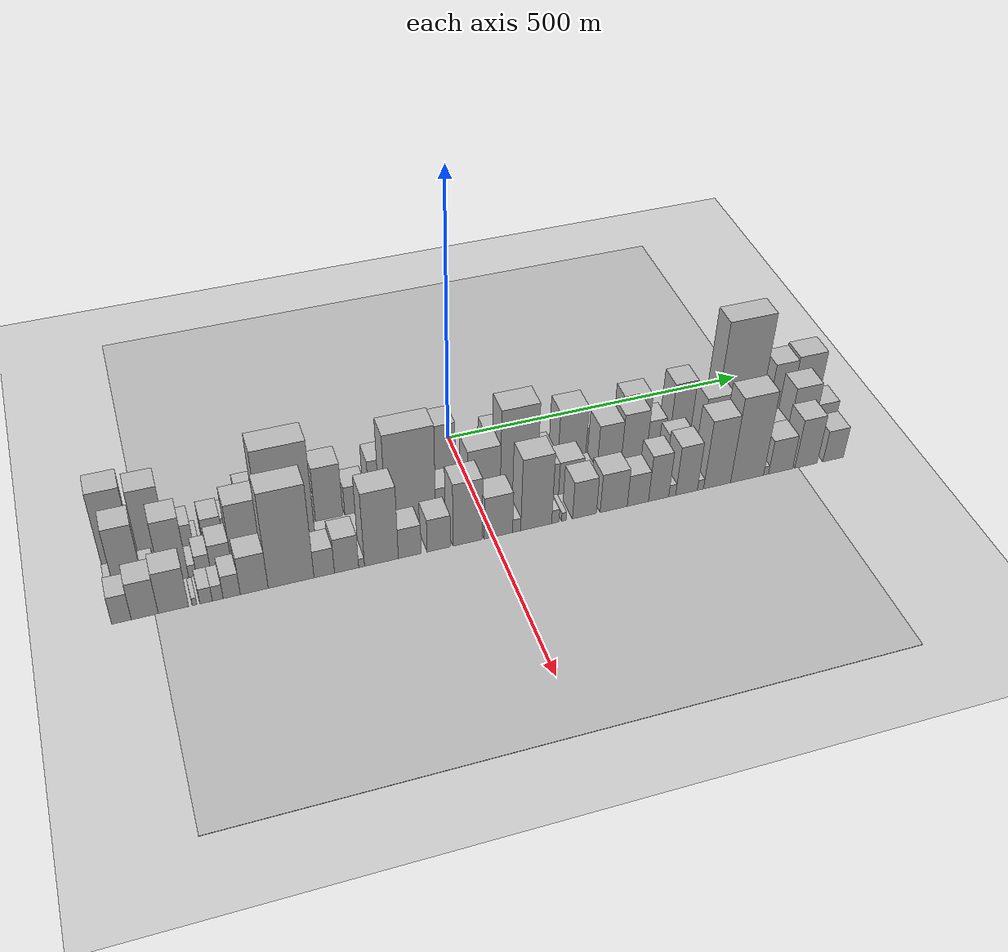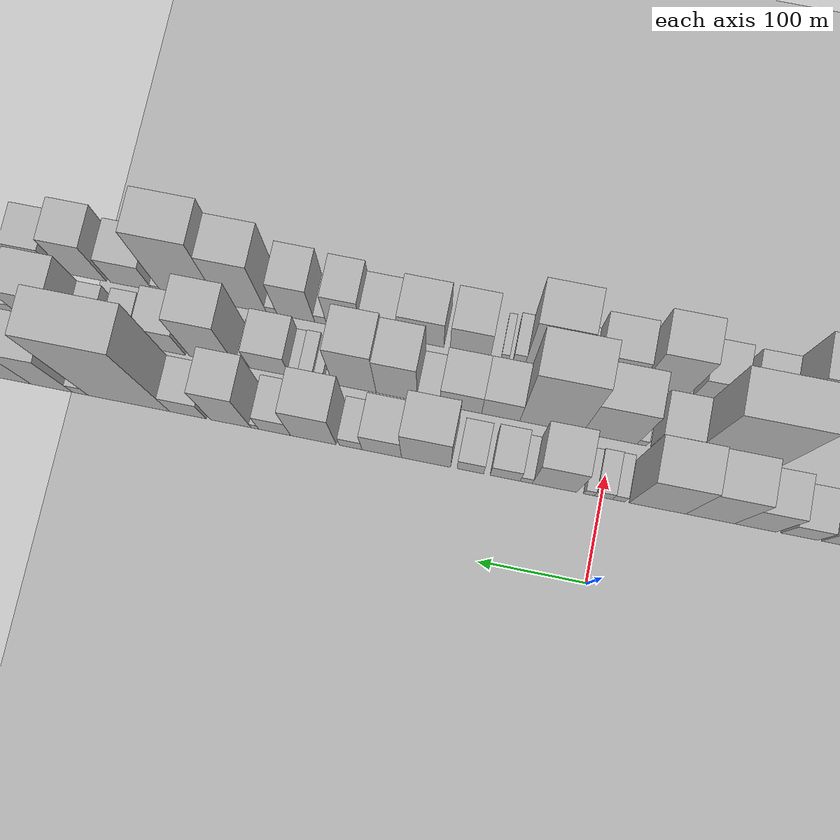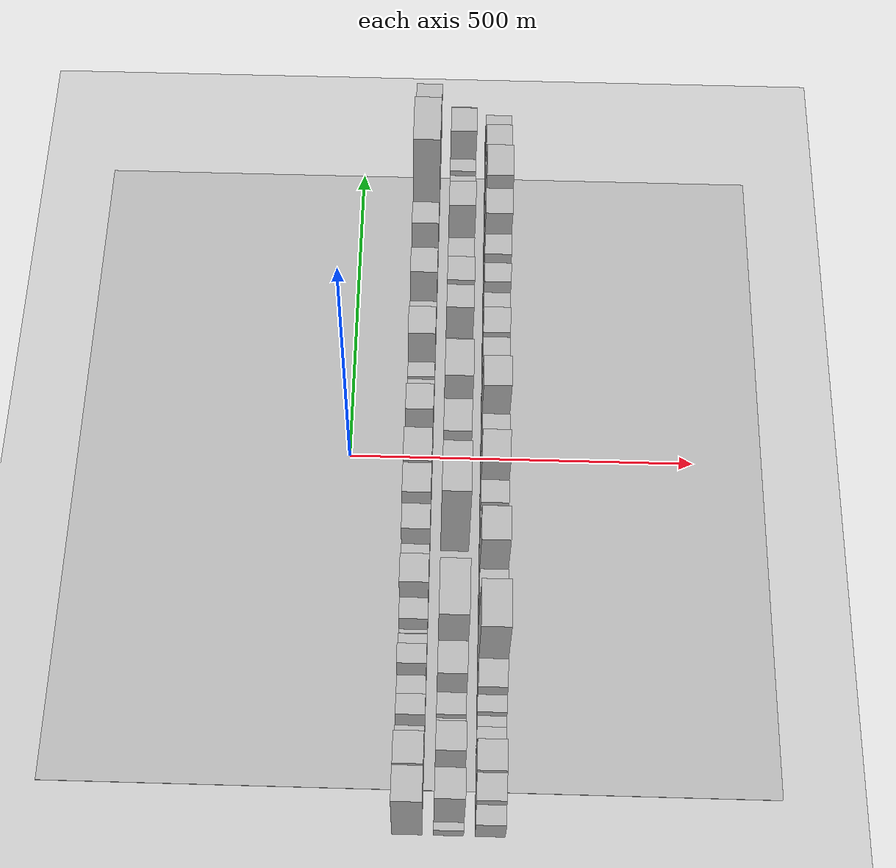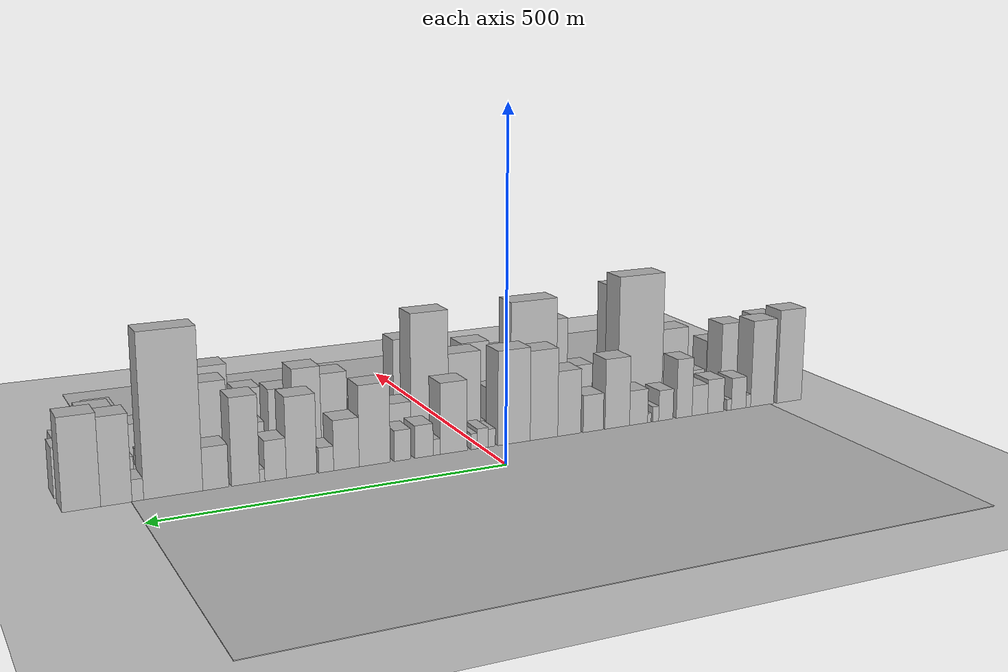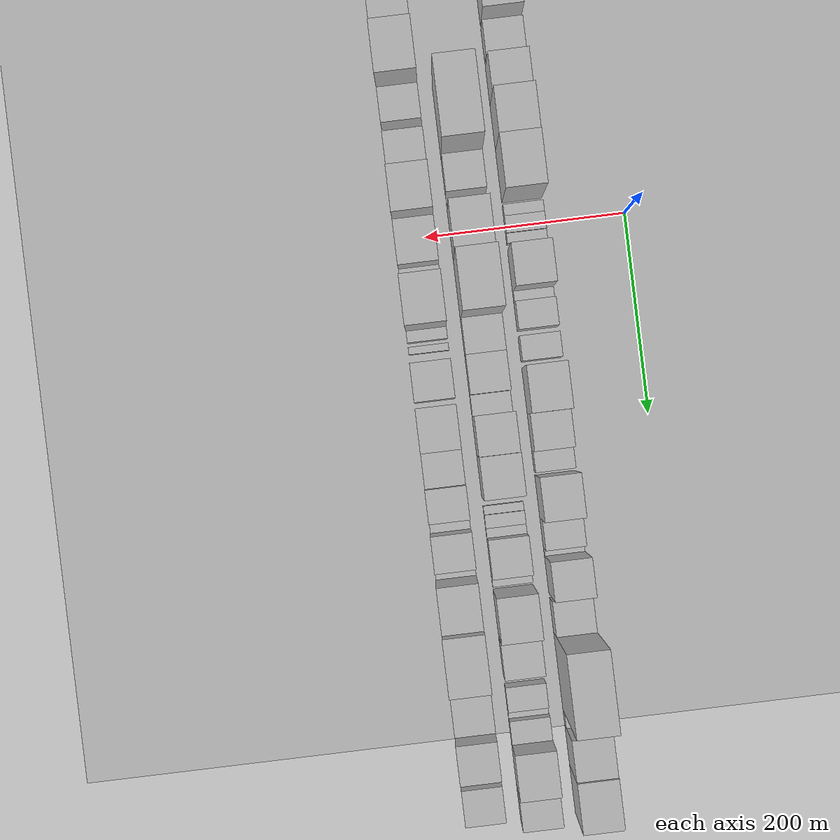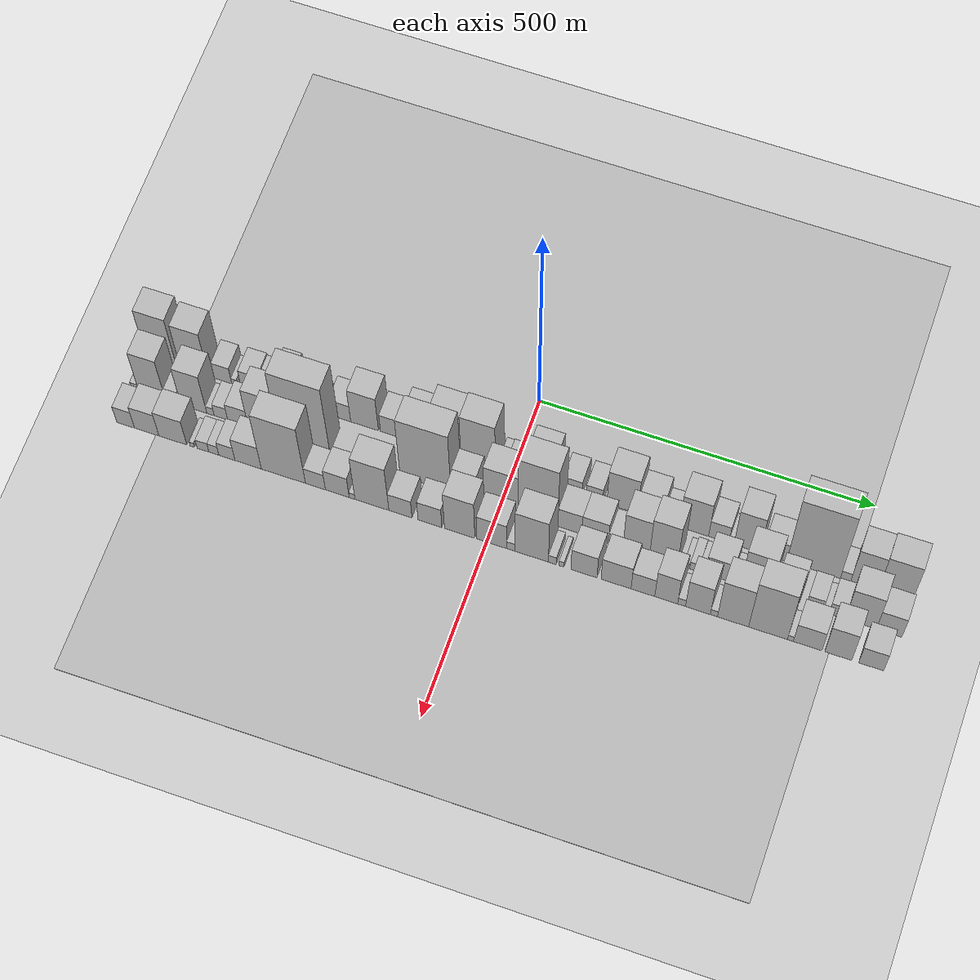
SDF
<?xml version="1.0" encoding="utf-8"?>

<sdf version="1.6">

   <world name="default">

      <gui fullscreen="0">

         <camera name="user_camera">

            <pose>-15 0 4.57585 0 0 0</pose>

            <view_controller>orbit</view_controller>

         </camera>

      </gui>

      <scene>

         <sky>

           <clouds>

             <speed>12</speed>

           </clouds>

         </sky>

         <ambient>0.4 0.4 0.4 1</ambient>

         <background>0.7 0.7 0.7 1</background>

         <shadows>1</shadows>

      </scene>

      <gravity>0 0 -9.8066</gravity>

      <magnetic_field>6e-06 2.3e-05 -4.2e-05</magnetic_field>

      <physics default="0" name="default_physics" type="ode">

         <ode>

            <solver>

               <type>quick</type>

               <iters>10</iters>

               <sor>1.0</sor>

               <use_dynamic_moi_rescaling>0</use_dynamic_moi_rescaling>

            </solver>

            <constraints>

               <cfm>0</cfm>

               <erp>0.2</erp>

               <contact_max_correcting_vel>100</contact_max_correcting_vel>

               <contact_surface_layer>0.001</contact_surface_layer>

            </constraints>

         </ode>

         <max_step_size>0.004</max_step_size>

         <real_time_factor>1</real_time_factor>

         <real_time_update_rate>250</real_time_update_rate>

      </physics>

      <light name="sun" type="directional">

         <cast_shadows>1</cast_shadows>

         <pose>0 0 10 0 0 0</pose>

         <diffuse>0.8 0.8 0.8 1</diffuse>

         <specular>0.2 0.2 0.2 1</specular>

         <attenuation>

            <range>1000</range>

            <constant>0.9</constant>

            <linear>0.01</linear>

            <quadratic>0.001</quadratic>

         </attenuation>

         <direction>-0.5 0.1 -0.9</direction>

      </light>

      <include>

         <name>ground_plane_1</name>

         <uri>model://HANNAS_ground_plane</uri>

         <pose>0 0 0  0 0 0</pose>

      </include>

      <include>

         <name>ground_plane_2</name>

         <uri>model://HANNAS_ground_plane</uri>

         <pose>100 0 0  0 0 0</pose>

      </include>

      <model name="building_1">

         <static>1</static>

         <pose frame="">100.0000 -536.4117 0 0.000000 0.000000 0.000000</pose>

         <link name="link">

            <pose frame="">0 0 75.00 0 0 0</pose>

            <collision name="collision">

               <geometry>

                  <box>

                     <size>40.0000 47.1765 150.0000</size>

                  </box>

               </geometry>

               <max_contacts>10</max_contacts>

               <surface>

                  <contact>

                     <ode/>

                  </contact>

                  <bounce/>

                  <friction>

                     <torsional>

                        <ode/>

                     </torsional>

                     <ode/>

                  </friction>

               </surface>

            </collision>

            <visual name="visual">

               <cast_shadows>0</cast_shadows>

               <geometry>

                  <box>

                     <size>40.0000 47.1765 150.0000</size>

                  </box>

               </geometry>

               <material>

                  <script>

                     <uri>model://HANNAS_wall/materials/scripts</uri>

                     <uri>model://HANNAS_wall/materials/textures</uri>

                     <name>vrc/HANNAS_wall</name>

                  </script>

               </material>

            </visual>

            <self_collide>0</self_collide>

            <enable_wind>0</enable_wind>

            <kinematic>0</kinematic>

         </link>

      </model>

      <model name="building_2">

         <static>1</static>

         <pose frame="">100.0000 -484.9652 0 0.000000 0.000000 0.000000</pose>

         <link name="link">

            <pose frame="">0 0 69.00 0 0 0</pose>

            <collision name="collision">

               <geometry>

                  <box>

                     <size>40.0000 43.7165 138.0000</size>

                  </box>

               </geometry>

               <max_contacts>10</max_contacts>

               <surface>

                  <contact>

                     <ode/>

                  </contact>

                  <bounce/>

                  <friction>

                     <torsional>

                        <ode/>

                     </torsional>

                     <ode/>

                  </friction>

               </surface>

            </collision>

            <visual name="visual">

               <cast_shadows>0</cast_shadows>

               <geometry>

                  <box>

                     <size>40.0000 43.7165 138.0000</size>

                  </box>

               </geometry>

               <material>

                  <script>

                     <uri>model://HANNAS_wall/materials/scripts</uri>

                     <uri>model://HANNAS_wall/materials/textures</uri>

                     <name>vrc/HANNAS_wall</name>

                  </script>

               </material>

            </visual>

            <self_collide>0</self_collide>

            <enable_wind>0</enable_wind>

            <kinematic>0</kinematic>

         </link>

      </model>

      <model name="building_3">

         <static>1</static>

         <pose frame="">100.0000 -458.6917 0 0.000000 0.000000 0.000000</pose>

         <link name="link">

            <pose frame="">0 0 10.50 0 0 0</pose>

            <collision name="collision">

               <geometry>

                  <box>

                     <size>40.0000 8.8305 21.0000</size>

                  </box>

               </geometry>

               <max_contacts>10</max_contacts>

               <surface>

                  <contact>

                     <ode/>

                  </contact>

                  <bounce/>

                  <friction>

                     <torsional>

                        <ode/>

                     </torsional>

                     <ode/>

                  </friction>

               </surface>

            </collision>

            <visual name="visual">

               <cast_shadows>0</cast_shadows>

               <geometry>

                  <box>

                     <size>40.0000 8.8305 21.0000</size>

                  </box>

               </geometry>

               <material>

                  <script>

                     <uri>model://HANNAS_wall/materials/scripts</uri>

                     <uri>model://HANNAS_wall/materials/textures</uri>

                     <name>vrc/HANNAS_wall</name>

                  </script>

               </material>

            </visual>

            <self_collide>0</self_collide>

            <enable_wind>0</enable_wind>

            <kinematic>0</kinematic>

         </link>

      </model>

      <model name="building_4">

         <static>1</static>

         <pose frame="">100.0000 -440.6678 0 0.000000 0.000000 0.000000</pose>

         <link name="link">

            <pose frame="">0 0 25.50 0 0 0</pose>

            <collision name="collision">

               <geometry>

                  <box>

                     <size>40.0000 27.2174 51.0000</size>

                  </box>

               </geometry>

               <max_contacts>10</max_contacts>

               <surface>

                  <contact>

                     <ode/>

                  </contact>

                  <bounce/>

                  <friction>

                     <torsional>

                        <ode/>

                     </torsional>

                     <ode/>

                  </friction>

               </surface>

            </collision>

            <visual name="visual">

               <cast_shadows>0</cast_shadows>

               <geometry>

                  <box>

                     <size>40.0000 27.2174 51.0000</size>

                  </box>

               </geometry>

               <material>

                  <script>

                     <uri>model://HANNAS_wall/materials/scripts</uri>

                     <uri>model://HANNAS_wall/materials/textures</uri>

                     <name>vrc/HANNAS_wall</name>

                  </script>

               </material>

            </visual>

            <self_collide>0</self_collide>

            <enable_wind>0</enable_wind>

            <kinematic>0</kinematic>

         </link>

      </model>

      <model name="building_5">

         <static>1</static>

         <pose frame="">100.0000 -422.9200 0 0.000000 0.000000 0.000000</pose>

         <link name="link">

            <pose frame="">0 0 9.00 0 0 0</pose>

            <collision name="collision">

               <geometry>

                  <box>

                     <size>40.0000 8.2782 18.0000</size>

                  </box>

               </geometry>

               <max_contacts>10</max_contacts>

               <surface>

                  <contact>

                     <ode/>

                  </contact>

                  <bounce/>

                  <friction>

                     <torsional>

                        <ode/>

                     </torsional>

                     <ode/>

                  </friction>

               </surface>

            </collision>

            <visual name="visual">

               <cast_shadows>0</cast_shadows>

               <geometry>

                  <box>

                     <size>40.0000 8.2782 18.0000</size>

                  </box>

               </geometry>

               <material>

                  <script>

                     <uri>model://HANNAS_wall/materials/scripts</uri>

                     <uri>model://HANNAS_wall/materials/textures</uri>

                     <name>vrc/HANNAS_wall</name>

                  </script>

               </material>

            </visual>

            <self_collide>0</self_collide>

            <enable_wind>0</enable_wind>

            <kinematic>0</kinematic>

         </link>

      </model>

      <model name="building_6">

         <static>1</static>

         <pose frame="">100.0000 -398.1051 0 0.000000 0.000000 0.000000</pose>

         <link name="link">

            <pose frame="">0 0 27.00 0 0 0</pose>

            <collision name="collision">

               <geometry>

                  <box>

                     <size>40.0000 29.3515 54.0000</size>

                  </box>

               </geometry>

               <max_contacts>10</max_contacts>

               <surface>

                  <contact>

                     <ode/>

                  </contact>

                  <bounce/>

                  <friction>

                     <torsional>

                        <ode/>

                     </torsional>

                     <ode/>

                  </friction>

               </surface>

            </collision>

            <visual name="visual">

               <cast_shadows>0</cast_shadows>

               <geometry>

                  <box>

                     <size>40.0000 29.3515 54.0000</size>

                  </box>

               </geometry>

               <material>

                  <script>

                     <uri>model://HANNAS_wall/materials/scripts</uri>

                     <uri>model://HANNAS_wall/materials/textures</uri>

                     <name>vrc/HANNAS_wall</name>

                  </script>

               </material>

            </visual>

            <self_collide>0</self_collide>

            <enable_wind>0</enable_wind>

            <kinematic>0</kinematic>

         </link>

      </model>

      <model name="building_7">

         <static>1</static>

         <pose frame="">100.0000 -369.2697 0 0.000000 0.000000 0.000000</pose>

         <link name="link">

            <pose frame="">0 0 24.00 0 0 0</pose>

            <collision name="collision">

               <geometry>

                  <box>

                     <size>40.0000 28.3194 48.0000</size>

                  </box>

               </geometry>

               <max_contacts>10</max_contacts>

               <surface>

                  <contact>

                     <ode/>

                  </contact>

                  <bounce/>

                  <friction>

                     <torsional>

                        <ode/>

                     </torsional>

                     <ode/>

                  </friction>

               </surface>

            </collision>

            <visual name="visual">

               <cast_shadows>0</cast_shadows>

               <geometry>

                  <box>

                     <size>40.0000 28.3194 48.0000</size>

                  </box>

               </geometry>

               <material>

                  <script>

                     <uri>model://HANNAS_wall/materials/scripts</uri>

                     <uri>model://HANNAS_wall/materials/textures</uri>

                     <name>vrc/HANNAS_wall</name>

                  </script>

               </material>

            </visual>

            <self_collide>0</self_collide>

            <enable_wind>0</enable_wind>

            <kinematic>0</kinematic>

         </link>

      </model>

      <model name="building_8">

         <static>1</static>

         <pose frame="">100.0000 -340.9920 0 0.000000 0.000000 0.000000</pose>

         <link name="link">

            <pose frame="">0 0 46.50 0 0 0</pose>

            <collision name="collision">

               <geometry>

                  <box>

                     <size>40.0000 28.2359 93.0000</size>

                  </box>

               </geometry>

               <max_contacts>10</max_contacts>

               <surface>

                  <contact>

                     <ode/>

                  </contact>

                  <bounce/>

                  <friction>

                     <torsional>

                        <ode/>

                     </torsional>

                     <ode/>

                  </friction>

               </surface>

            </collision>

            <visual name="visual">

               <cast_shadows>0</cast_shadows>

               <geometry>

                  <box>

                     <size>40.0000 28.2359 93.0000</size>

                  </box>

               </geometry>

               <material>

                  <script>

                     <uri>model://HANNAS_wall/materials/scripts</uri>

                     <uri>model://HANNAS_wall/materials/textures</uri>

                     <name>vrc/HANNAS_wall</name>

                  </script>

               </material>

            </visual>

            <self_collide>0</self_collide>

            <enable_wind>0</enable_wind>

            <kinematic>0</kinematic>

         </link>

      </model>

      <model name="building_9">

         <static>1</static>

         <pose frame="">100.0000 -308.1713 0 0.000000 0.000000 0.000000</pose>

         <link name="link">

            <pose frame="">0 0 24.00 0 0 0</pose>

            <collision name="collision">

               <geometry>

                  <box>

                     <size>40.0000 25.4055 48.0000</size>

                  </box>

               </geometry>

               <max_contacts>10</max_contacts>

               <surface>

                  <contact>

                     <ode/>

                  </contact>

                  <bounce/>

                  <friction>

                     <torsional>

                        <ode/>

                     </torsional>

                     <ode/>

                  </friction>

               </surface>

            </collision>

            <visual name="visual">

               <cast_shadows>0</cast_shadows>

               <geometry>

                  <box>

                     <size>40.0000 25.4055 48.0000</size>

                  </box>

               </geometry>

               <material>

                  <script>

                     <uri>model://HANNAS_wall/materials/scripts</uri>

                     <uri>model://HANNAS_wall/materials/textures</uri>

                     <name>vrc/HANNAS_wall</name>

                  </script>

               </material>

            </visual>

            <self_collide>0</self_collide>

            <enable_wind>0</enable_wind>

            <kinematic>0</kinematic>

         </link>

      </model>

      <model name="building_10">

         <static>1</static>

         <pose frame="">100.0000 -290.2716 0 0.000000 0.000000 0.000000</pose>

         <link name="link">

            <pose frame="">0 0 12.00 0 0 0</pose>

            <collision name="collision">

               <geometry>

                  <box>

                     <size>40.0000 10.3939 24.0000</size>

                  </box>

               </geometry>

               <max_contacts>10</max_contacts>

               <surface>

                  <contact>

                     <ode/>

                  </contact>

                  <bounce/>

                  <friction>

                     <torsional>

                        <ode/>

                     </torsional>

                     <ode/>

                  </friction>

               </surface>

            </collision>

            <visual name="visual">

               <cast_shadows>0</cast_shadows>

               <geometry>

                  <box>

                     <size>40.0000 10.3939 24.0000</size>

                  </box>

               </geometry>

               <material>

                  <script>

                     <uri>model://HANNAS_wall/materials/scripts</uri>

                     <uri>model://HANNAS_wall/materials/textures</uri>

                     <name>vrc/HANNAS_wall</name>

                  </script>

               </material>

            </visual>

            <self_collide>0</self_collide>

            <enable_wind>0</enable_wind>

            <kinematic>0</kinematic>

         </link>

      </model>

      <model name="building_11">

         <static>1</static>

         <pose frame="">100.0000 -278.9836 0 0.000000 0.000000 0.000000</pose>

         <link name="link">

            <pose frame="">0 0 7.50 0 0 0</pose>

            <collision name="collision">

               <geometry>

                  <box>

                     <size>40.0000 6.1822 15.0000</size>

                  </box>

               </geometry>

               <max_contacts>10</max_contacts>

               <surface>

                  <contact>

                     <ode/>

                  </contact>

                  <bounce/>

                  <friction>

                     <torsional>

                        <ode/>

                     </torsional>

                     <ode/>

                  </friction>

               </surface>

            </collision>

            <visual name="visual">

               <cast_shadows>0</cast_shadows>

               <geometry>

                  <box>

                     <size>40.0000 6.1822 15.0000</size>

                  </box>

               </geometry>

               <material>

                  <script>

                     <uri>model://HANNAS_wall/materials/scripts</uri>

                     <uri>model://HANNAS_wall/materials/textures</uri>

                     <name>vrc/HANNAS_wall</name>

                  </script>

               </material>

            </visual>

            <self_collide>0</self_collide>

            <enable_wind>0</enable_wind>

            <kinematic>0</kinematic>

         </link>

      </model>

      <model name="building_12">

         <static>1</static>

         <pose frame="">100.0000 -260.1429 0 0.000000 0.000000 0.000000</pose>

         <link name="link">

            <pose frame="">0 0 27.00 0 0 0</pose>

            <collision name="collision">

               <geometry>

                  <box>

                     <size>40.0000 31.4992 54.0000</size>

                  </box>

               </geometry>

               <max_contacts>10</max_contacts>

               <surface>

                  <contact>

                     <ode/>

                  </contact>

                  <bounce/>

                  <friction>

                     <torsional>

                        <ode/>

                     </torsional>

                     <ode/>

                  </friction>

               </surface>

            </collision>

            <visual name="visual">

               <cast_shadows>0</cast_shadows>

               <geometry>

                  <box>

                     <size>40.0000 31.4992 54.0000</size>

                  </box>

               </geometry>

               <material>

                  <script>

                     <uri>model://HANNAS_wall/materials/scripts</uri>

                     <uri>model://HANNAS_wall/materials/textures</uri>

                     <name>vrc/HANNAS_wall</name>

                  </script>

               </material>

            </visual>

            <self_collide>0</self_collide>

            <enable_wind>0</enable_wind>

            <kinematic>0</kinematic>

         </link>

      </model>

      <model name="building_13">

         <static>1</static>

         <pose frame="">100.0000 -223.2417 0 0.000000 0.000000 0.000000</pose>

         <link name="link">

            <pose frame="">0 0 54.00 0 0 0</pose>

            <collision name="collision">

               <geometry>

                  <box>

                     <size>40.0000 42.3031 108.0000</size>

                  </box>

               </geometry>

               <max_contacts>10</max_contacts>

               <surface>

                  <contact>

                     <ode/>

                  </contact>

                  <bounce/>

                  <friction>

                     <torsional>

                        <ode/>

                     </torsional>

                     <ode/>

                  </friction>

               </surface>

            </collision>

            <visual name="visual">

               <cast_shadows>0</cast_shadows>

               <geometry>

                  <box>

                     <size>40.0000 42.3031 108.0000</size>

                  </box>

               </geometry>

               <material>

                  <script>

                     <uri>model://HANNAS_wall/materials/scripts</uri>

                     <uri>model://HANNAS_wall/materials/textures</uri>

                     <name>vrc/HANNAS_wall</name>

                  </script>

               </material>

            </visual>

            <self_collide>0</self_collide>

            <enable_wind>0</enable_wind>

            <kinematic>0</kinematic>

         </link>

      </model>

      <model name="building_14">

         <static>1</static>

         <pose frame="">100.0000 -182.0863 0 0.000000 0.000000 0.000000</pose>

         <link name="link">

            <pose frame="">0 0 28.50 0 0 0</pose>

            <collision name="collision">

               <geometry>

                  <box>

                     <size>40.0000 34.0078 57.0000</size>

                  </box>

               </geometry>

               <max_contacts>10</max_contacts>

               <surface>

                  <contact>

                     <ode/>

                  </contact>

                  <bounce/>

                  <friction>

                     <torsional>

                        <ode/>

                     </torsional>

                     <ode/>

                  </friction>

               </surface>

            </collision>

            <visual name="visual">

               <cast_shadows>0</cast_shadows>

               <geometry>

                  <box>

                     <size>40.0000 34.0078 57.0000</size>

                  </box>

               </geometry>

               <material>

                  <script>

                     <uri>model://HANNAS_wall/materials/scripts</uri>

                     <uri>model://HANNAS_wall/materials/textures</uri>

                     <name>vrc/HANNAS_wall</name>

                  </script>

               </material>

            </visual>

            <self_collide>0</self_collide>

            <enable_wind>0</enable_wind>

            <kinematic>0</kinematic>

         </link>

      </model>

      <model name="building_15">

         <static>1</static>

         <pose frame="">100.0000 -141.8271 0 0.000000 0.000000 0.000000</pose>

         <link name="link">

            <pose frame="">0 0 49.50 0 0 0</pose>

            <collision name="collision">

               <geometry>

                  <box>

                     <size>40.0000 38.5107 99.0000</size>

                  </box>

               </geometry>

               <max_contacts>10</max_contacts>

               <surface>

                  <contact>

                     <ode/>

                  </contact>

                  <bounce/>

                  <friction>

                     <torsional>

                        <ode/>

                     </torsional>

                     <ode/>

                  </friction>

               </surface>

            </collision>

            <visual name="visual">

               <cast_shadows>0</cast_shadows>

               <geometry>

                  <box>

                     <size>40.0000 38.5107 99.0000</size>

                  </box>

               </geometry>

               <material>

                  <script>

                     <uri>model://HANNAS_wall/materials/scripts</uri>

                     <uri>model://HANNAS_wall/materials/textures</uri>

                     <name>vrc/HANNAS_wall</name>

                  </script>

               </material>

            </visual>

            <self_collide>0</self_collide>

            <enable_wind>0</enable_wind>

            <kinematic>0</kinematic>

         </link>

      </model>

      <model name="building_16">

         <static>1</static>

         <pose frame="">100.0000 -100.0000 0 0.000000 0.000000 0.000000</pose>

         <link name="link">

            <pose frame="">0 0 67.50 0 0 0</pose>

            <collision name="collision">

               <geometry>

                  <box>

                     <size>40.0000 45.1434 135.0000</size>

                  </box>

               </geometry>

               <max_contacts>10</max_contacts>

               <surface>

                  <contact>

                     <ode/>

                  </contact>

                  <bounce/>

                  <friction>

                     <torsional>

                        <ode/>

                     </torsional>

                     <ode/>

                  </friction>

               </surface>

            </collision>

            <visual name="visual">

               <cast_shadows>0</cast_shadows>

               <geometry>

                  <box>

                     <size>40.0000 45.1434 135.0000</size>

                  </box>

               </geometry>

               <material>

                  <script>

                     <uri>model://HANNAS_wall/materials/scripts</uri>

                     <uri>model://HANNAS_wall/materials/textures</uri>

                     <name>vrc/HANNAS_wall</name>

                  </script>

               </material>

            </visual>

            <self_collide>0</self_collide>

            <enable_wind>0</enable_wind>

            <kinematic>0</kinematic>

         </link>

      </model>

      <model name="building_17">

         <static>1</static>

         <pose frame="">100.0000 -51.3280 0 0.000000 0.000000 0.000000</pose>

         <link name="link">

            <pose frame="">0 0 70.50 0 0 0</pose>

            <collision name="collision">

               <geometry>

                  <box>

                     <size>40.0000 52.2006 141.0000</size>

                  </box>

               </geometry>

               <max_contacts>10</max_contacts>

               <surface>

                  <contact>

                     <ode/>

                  </contact>

                  <bounce/>

                  <friction>

                     <torsional>

                        <ode/>

                     </torsional>

                     <ode/>

                  </friction>

               </surface>

            </collision>

            <visual name="visual">

               <cast_shadows>0</cast_shadows>

               <geometry>

                  <box>

                     <size>40.0000 52.2006 141.0000</size>

                  </box>

               </geometry>

               <material>

                  <script>

                     <uri>model://HANNAS_wall/materials/scripts</uri>

                     <uri>model://HANNAS_wall/materials/textures</uri>

                     <name>vrc/HANNAS_wall</name>

                  </script>

               </material>

            </visual>

            <self_collide>0</self_collide>

            <enable_wind>0</enable_wind>

            <kinematic>0</kinematic>

         </link>

      </model>

      <model name="building_18">

         <static>1</static>

         <pose frame="">100.0000 -15.4119 0 0.000000 0.000000 0.000000</pose>

         <link name="link">

            <pose frame="">0 0 13.50 0 0 0</pose>

            <collision name="collision">

               <geometry>

                  <box>

                     <size>40.0000 11.6316 27.0000</size>

                  </box>

               </geometry>

               <max_contacts>10</max_contacts>

               <surface>

                  <contact>

                     <ode/>

                  </contact>

                  <bounce/>

                  <friction>

                     <torsional>

                        <ode/>

                     </torsional>

                     <ode/>

                  </friction>

               </surface>

            </collision>

            <visual name="visual">

               <cast_shadows>0</cast_shadows>

               <geometry>

                  <box>

                     <size>40.0000 11.6316 27.0000</size>

                  </box>

               </geometry>

               <material>

                  <script>

                     <uri>model://HANNAS_wall/materials/scripts</uri>

                     <uri>model://HANNAS_wall/materials/textures</uri>

                     <name>vrc/HANNAS_wall</name>

                  </script>

               </material>

            </visual>

            <self_collide>0</self_collide>

            <enable_wind>0</enable_wind>

            <kinematic>0</kinematic>

         </link>

      </model>

      <model name="building_19">

         <static>1</static>

         <pose frame="">100.0000 -1.0945 0 0.000000 0.000000 0.000000</pose>

         <link name="link">

            <pose frame="">0 0 15.00 0 0 0</pose>

            <collision name="collision">

               <geometry>

                  <box>

                     <size>40.0000 17.0032 30.0000</size>

                  </box>

               </geometry>

               <max_contacts>10</max_contacts>

               <surface>

                  <contact>

                     <ode/>

                  </contact>

                  <bounce/>

                  <friction>

                     <torsional>

                        <ode/>

                     </torsional>

                     <ode/>

                  </friction>

               </surface>

            </collision>

            <visual name="visual">

               <cast_shadows>0</cast_shadows>

               <geometry>

                  <box>

                     <size>40.0000 17.0032 30.0000</size>

                  </box>

               </geometry>

               <material>

                  <script>

                     <uri>model://HANNAS_wall/materials/scripts</uri>

                     <uri>model://HANNAS_wall/materials/textures</uri>

                     <name>vrc/HANNAS_wall</name>

                  </script>

               </material>

            </visual>

            <self_collide>0</self_collide>

            <enable_wind>0</enable_wind>

            <kinematic>0</kinematic>

         </link>

      </model>

      <model name="building_20">

         <static>1</static>

         <pose frame="">100.0000 12.2904 0 0.000000 0.000000 0.000000</pose>

         <link name="link">

            <pose frame="">0 0 12.00 0 0 0</pose>

            <collision name="collision">

               <geometry>

                  <box>

                     <size>40.0000 9.7668 24.0000</size>

                  </box>

               </geometry>

               <max_contacts>10</max_contacts>

               <surface>

                  <contact>

                     <ode/>

                  </contact>

                  <bounce/>

                  <friction>

                     <torsional>

                        <ode/>

                     </torsional>

                     <ode/>

                  </friction>

               </surface>

            </collision>

            <visual name="visual">

               <cast_shadows>0</cast_shadows>

               <geometry>

                  <box>

                     <size>40.0000 9.7668 24.0000</size>

                  </box>

               </geometry>

               <material>

                  <script>

                     <uri>model://HANNAS_wall/materials/scripts</uri>

                     <uri>model://HANNAS_wall/materials/textures</uri>

                     <name>vrc/HANNAS_wall</name>

                  </script>

               </material>

            </visual>

            <self_collide>0</self_collide>

            <enable_wind>0</enable_wind>

            <kinematic>0</kinematic>

         </link>

      </model>

      <model name="building_21">

         <static>1</static>

         <pose frame="">100.0000 44.0193 0 0.000000 0.000000 0.000000</pose>

         <link name="link">

            <pose frame="">0 0 52.50 0 0 0</pose>

            <collision name="collision">

               <geometry>

                  <box>

                     <size>40.0000 41.6909 105.0000</size>

                  </box>

               </geometry>

               <max_contacts>10</max_contacts>

               <surface>

                  <contact>

                     <ode/>

                  </contact>

                  <bounce/>

                  <friction>

                     <torsional>

                        <ode/>

                     </torsional>

                     <ode/>

                  </friction>

               </surface>

            </collision>

            <visual name="visual">

               <cast_shadows>0</cast_shadows>

               <geometry>

                  <box>

                     <size>40.0000 41.6909 105.0000</size>

                  </box>

               </geometry>

               <material>

                  <script>

                     <uri>model://HANNAS_wall/materials/scripts</uri>

                     <uri>model://HANNAS_wall/materials/textures</uri>

                     <name>vrc/HANNAS_wall</name>

                  </script>

               </material>

            </visual>

            <self_collide>0</self_collide>

            <enable_wind>0</enable_wind>

            <kinematic>0</kinematic>

         </link>

      </model>

      <model name="building_22">

         <static>1</static>

         <pose frame="">100.0000 70.4812 0 0.000000 0.000000 0.000000</pose>

         <link name="link">

            <pose frame="">0 0 12.00 0 0 0</pose>

            <collision name="collision">

               <geometry>

                  <box>

                     <size>40.0000 11.2330 24.0000</size>

                  </box>

               </geometry>

               <max_contacts>10</max_contacts>

               <surface>

                  <contact>

                     <ode/>

                  </contact>

                  <bounce/>

                  <friction>

                     <torsional>

                        <ode/>

                     </torsional>

                     <ode/>

                  </friction>

               </surface>

            </collision>

            <visual name="visual">

               <cast_shadows>0</cast_shadows>

               <geometry>

                  <box>

                     <size>40.0000 11.2330 24.0000</size>

                  </box>

               </geometry>

               <material>

                  <script>

                     <uri>model://HANNAS_wall/materials/scripts</uri>

                     <uri>model://HANNAS_wall/materials/textures</uri>

                     <name>vrc/HANNAS_wall</name>

                  </script>

               </material>

            </visual>

            <self_collide>0</self_collide>

            <enable_wind>0</enable_wind>

            <kinematic>0</kinematic>

         </link>

      </model>

      <model name="building_23">

         <static>1</static>

         <pose frame="">100.0000 90.1137 0 0.000000 0.000000 0.000000</pose>

         <link name="link">

            <pose frame="">0 0 24.00 0 0 0</pose>

            <collision name="collision">

               <geometry>

                  <box>

                     <size>40.0000 28.0321 48.0000</size>

                  </box>

               </geometry>

               <max_contacts>10</max_contacts>

               <surface>

                  <contact>

                     <ode/>

                  </contact>

                  <bounce/>

                  <friction>

                     <torsional>

                        <ode/>

                     </torsional>

                     <ode/>

                  </friction>

               </surface>

            </collision>

            <visual name="visual">

               <cast_shadows>0</cast_shadows>

               <geometry>

                  <box>

                     <size>40.0000 28.0321 48.0000</size>

                  </box>

               </geometry>

               <material>

                  <script>

                     <uri>model://HANNAS_wall/materials/scripts</uri>

                     <uri>model://HANNAS_wall/materials/textures</uri>

                     <name>vrc/HANNAS_wall</name>

                  </script>

               </material>

            </visual>

            <self_collide>0</self_collide>

            <enable_wind>0</enable_wind>

            <kinematic>0</kinematic>

         </link>

      </model>

      <model name="building_24">

         <static>1</static>

         <pose frame="">100.0000 122.5841 0 0.000000 0.000000 0.000000</pose>

         <link name="link">

            <pose frame="">0 0 22.50 0 0 0</pose>

            <collision name="collision">

               <geometry>

                  <box>

                     <size>40.0000 24.9087 45.0000</size>

                  </box>

               </geometry>

               <max_contacts>10</max_contacts>

               <surface>

                  <contact>

                     <ode/>

                  </contact>

                  <bounce/>

                  <friction>

                     <torsional>

                        <ode/>

                     </torsional>

                     <ode/>

                  </friction>

               </surface>

            </collision>

            <visual name="visual">

               <cast_shadows>0</cast_shadows>

               <geometry>

                  <box>

                     <size>40.0000 24.9087 45.0000</size>

                  </box>

               </geometry>

               <material>

                  <script>

                     <uri>model://HANNAS_wall/materials/scripts</uri>

                     <uri>model://HANNAS_wall/materials/textures</uri>

                     <name>vrc/HANNAS_wall</name>

                  </script>

               </material>

            </visual>

            <self_collide>0</self_collide>

            <enable_wind>0</enable_wind>

            <kinematic>0</kinematic>

         </link>

      </model>

      <model name="building_25">

         <static>1</static>

         <pose frame="">100.0000 164.0409 0 0.000000 0.000000 0.000000</pose>

         <link name="link">

            <pose frame="">0 0 58.50 0 0 0</pose>

            <collision name="collision">

               <geometry>

                  <box>

                     <size>40.0000 46.0048 117.0000</size>

                  </box>

               </geometry>

               <max_contacts>10</max_contacts>

               <surface>

                  <contact>

                     <ode/>

                  </contact>

                  <bounce/>

                  <friction>

                     <torsional>

                        <ode/>

                     </torsional>

                     <ode/>

                  </friction>

               </surface>

            </collision>

            <visual name="visual">

               <cast_shadows>0</cast_shadows>

               <geometry>

                  <box>

                     <size>40.0000 46.0048 117.0000</size>

                  </box>

               </geometry>

               <material>

                  <script>

                     <uri>model://HANNAS_wall/materials/scripts</uri>

                     <uri>model://HANNAS_wall/materials/textures</uri>

                     <name>vrc/HANNAS_wall</name>

                  </script>

               </material>

            </visual>

            <self_collide>0</self_collide>

            <enable_wind>0</enable_wind>

            <kinematic>0</kinematic>

         </link>

      </model>

      <model name="building_26">

         <static>1</static>

         <pose frame="">100.0000 205.5734 0 0.000000 0.000000 0.000000</pose>

         <link name="link">

            <pose frame="">0 0 36.00 0 0 0</pose>

            <collision name="collision">

               <geometry>

                  <box>

                     <size>40.0000 37.0601 72.0000</size>

                  </box>

               </geometry>

               <max_contacts>10</max_contacts>

               <surface>

                  <contact>

                     <ode/>

                  </contact>

                  <bounce/>

                  <friction>

                     <torsional>

                        <ode/>

                     </torsional>

                     <ode/>

                  </friction>

               </surface>

            </collision>

            <visual name="visual">

               <cast_shadows>0</cast_shadows>

               <geometry>

                  <box>

                     <size>40.0000 37.0601 72.0000</size>

                  </box>

               </geometry>

               <material>

                  <script>

                     <uri>model://HANNAS_wall/materials/scripts</uri>

                     <uri>model://HANNAS_wall/materials/textures</uri>

                     <name>vrc/HANNAS_wall</name>

                  </script>

               </material>

            </visual>

            <self_collide>0</self_collide>

            <enable_wind>0</enable_wind>

            <kinematic>0</kinematic>

         </link>

      </model>

      <model name="building_27">

         <static>1</static>

         <pose frame="">100.0000 234.7324 0 0.000000 0.000000 0.000000</pose>

         <link name="link">

            <pose frame="">0 0 18.00 0 0 0</pose>

            <collision name="collision">

               <geometry>

                  <box>

                     <size>40.0000 21.2580 36.0000</size>

                  </box>

               </geometry>

               <max_contacts>10</max_contacts>

               <surface>

                  <contact>

                     <ode/>

                  </contact>

                  <bounce/>

                  <friction>

                     <torsional>

                        <ode/>

                     </torsional>

                     <ode/>

                  </friction>

               </surface>

            </collision>

            <visual name="visual">

               <cast_shadows>0</cast_shadows>

               <geometry>

                  <box>

                     <size>40.0000 21.2580 36.0000</size>

                  </box>

               </geometry>

               <material>

                  <script>

                     <uri>model://HANNAS_wall/materials/scripts</uri>

                     <uri>model://HANNAS_wall/materials/textures</uri>

                     <name>vrc/HANNAS_wall</name>

                  </script>

               </material>

            </visual>

            <self_collide>0</self_collide>

            <enable_wind>0</enable_wind>

            <kinematic>0</kinematic>

         </link>

      </model>

      <model name="building_28">

         <static>1</static>

         <pose frame="">100.0000 269.9619 0 0.000000 0.000000 0.000000</pose>

         <link name="link">

            <pose frame="">0 0 57.00 0 0 0</pose>

            <collision name="collision">

               <geometry>

                  <box>

                     <size>40.0000 43.2010 114.0000</size>

                  </box>

               </geometry>

               <max_contacts>10</max_contacts>

               <surface>

                  <contact>

                     <ode/>

                  </contact>

                  <bounce/>

                  <friction>

                     <torsional>

                        <ode/>

                     </torsional>

                     <ode/>

                  </friction>

               </surface>

            </collision>

            <visual name="visual">

               <cast_shadows>0</cast_shadows>

               <geometry>

                  <box>

                     <size>40.0000 43.2010 114.0000</size>

                  </box>

               </geometry>

               <material>

                  <script>

                     <uri>model://HANNAS_wall/materials/scripts</uri>

                     <uri>model://HANNAS_wall/materials/textures</uri>

                     <name>vrc/HANNAS_wall</name>

                  </script>

               </material>

            </visual>

            <self_collide>0</self_collide>

            <enable_wind>0</enable_wind>

            <kinematic>0</kinematic>

         </link>

      </model>

      <model name="building_29">

         <static>1</static>

         <pose frame="">100.0000 306.5594 0 0.000000 0.000000 0.000000</pose>

         <link name="link">

            <pose frame="">0 0 28.50 0 0 0</pose>

            <collision name="collision">

               <geometry>

                  <box>

                     <size>40.0000 29.9941 57.0000</size>

                  </box>

               </geometry>

               <max_contacts>10</max_contacts>

               <surface>

                  <contact>

                     <ode/>

                  </contact>

                  <bounce/>

                  <friction>

                     <torsional>

                        <ode/>

                     </torsional>

                     <ode/>

                  </friction>

               </surface>

            </collision>

            <visual name="visual">

               <cast_shadows>0</cast_shadows>

               <geometry>

                  <box>

                     <size>40.0000 29.9941 57.0000</size>

                  </box>

               </geometry>

               <material>

                  <script>

                     <uri>model://HANNAS_wall/materials/scripts</uri>

                     <uri>model://HANNAS_wall/materials/textures</uri>

                     <name>vrc/HANNAS_wall</name>

                  </script>

               </material>

            </visual>

            <self_collide>0</self_collide>

            <enable_wind>0</enable_wind>

            <kinematic>0</kinematic>

         </link>

      </model>

      <model name="building_30">

         <static>1</static>

         <pose frame="">100.0000 325.1949 0 0.000000 0.000000 0.000000</pose>

         <link name="link">

            <pose frame="">0 0 9.00 0 0 0</pose>

            <collision name="collision">

               <geometry>

                  <box>

                     <size>40.0000 7.2768 18.0000</size>

                  </box>

               </geometry>

               <max_contacts>10</max_contacts>

               <surface>

                  <contact>

                     <ode/>

                  </contact>

                  <bounce/>

                  <friction>

                     <torsional>

                        <ode/>

                     </torsional>

                     <ode/>

                  </friction>

               </surface>

            </collision>

            <visual name="visual">

               <cast_shadows>0</cast_shadows>

               <geometry>

                  <box>

                     <size>40.0000 7.2768 18.0000</size>

                  </box>

               </geometry>

               <material>

                  <script>

                     <uri>model://HANNAS_wall/materials/scripts</uri>

                     <uri>model://HANNAS_wall/materials/textures</uri>

                     <name>vrc/HANNAS_wall</name>

                  </script>

               </material>

            </visual>

            <self_collide>0</self_collide>

            <enable_wind>0</enable_wind>

            <kinematic>0</kinematic>

         </link>

      </model>

      <model name="building_31">

         <static>1</static>

         <pose frame="">100.0000 347.9700 0 0.000000 0.000000 0.000000</pose>

         <link name="link">

            <pose frame="">0 0 61.50 0 0 0</pose>

            <collision name="collision">

               <geometry>

                  <box>

                     <size>40.0000 38.2735 123.0000</size>

                  </box>

               </geometry>

               <max_contacts>10</max_contacts>

               <surface>

                  <contact>

                     <ode/>

                  </contact>

                  <bounce/>

                  <friction>

                     <torsional>

                        <ode/>

                     </torsional>

                     <ode/>

                  </friction>

               </surface>

            </collision>

            <visual name="visual">

               <cast_shadows>0</cast_shadows>

               <geometry>

                  <box>

                     <size>40.0000 38.2735 123.0000</size>

                  </box>

               </geometry>

               <material>

                  <script>

                     <uri>model://HANNAS_wall/materials/scripts</uri>

                     <uri>model://HANNAS_wall/materials/textures</uri>

                     <name>vrc/HANNAS_wall</name>

                  </script>

               </material>

            </visual>

            <self_collide>0</self_collide>

            <enable_wind>0</enable_wind>

            <kinematic>0</kinematic>

         </link>

      </model>

      <model name="building_32">

         <static>1</static>

         <pose frame="">100.0000 388.5789 0 0.000000 0.000000 0.000000</pose>

         <link name="link">

            <pose frame="">0 0 30.00 0 0 0</pose>

            <collision name="collision">

               <geometry>

                  <box>

                     <size>40.0000 34.9442 60.0000</size>

                  </box>

               </geometry>

               <max_contacts>10</max_contacts>

               <surface>

                  <contact>

                     <ode/>

                  </contact>

                  <bounce/>

                  <friction>

                     <torsional>

                        <ode/>

                     </torsional>

                     <ode/>

                  </friction>

               </surface>

            </collision>

            <visual name="visual">

               <cast_shadows>0</cast_shadows>

               <geometry>

                  <box>

                     <size>40.0000 34.9442 60.0000</size>

                  </box>

               </geometry>

               <material>

                  <script>

                     <uri>model://HANNAS_wall/materials/scripts</uri>

                     <uri>model://HANNAS_wall/materials/textures</uri>

                     <name>vrc/HANNAS_wall</name>

                  </script>

               </material>

            </visual>

            <self_collide>0</self_collide>

            <enable_wind>0</enable_wind>

            <kinematic>0</kinematic>

         </link>

      </model>

      <model name="building_33">

         <static>1</static>

         <pose frame="">100.0000 444.9946 0 0.000000 0.000000 0.000000</pose>

         <link name="link">

            <pose frame="">0 0 112.50 0 0 0</pose>

            <collision name="collision">

               <geometry>

                  <box>

                     <size>40.0000 77.8872 225.0000</size>

                  </box>

               </geometry>

               <max_contacts>10</max_contacts>

               <surface>

                  <contact>

                     <ode/>

                  </contact>

                  <bounce/>

                  <friction>

                     <torsional>

                        <ode/>

                     </torsional>

                     <ode/>

                  </friction>

               </surface>

            </collision>

            <visual name="visual">

               <cast_shadows>0</cast_shadows>

               <geometry>

                  <box>

                     <size>40.0000 77.8872 225.0000</size>

                  </box>

               </geometry>

               <material>

                  <script>

                     <uri>model://HANNAS_wall/materials/scripts</uri>

                     <uri>model://HANNAS_wall/materials/textures</uri>

                     <name>vrc/HANNAS_wall</name>

                  </script>

               </material>

            </visual>

            <self_collide>0</self_collide>

            <enable_wind>0</enable_wind>

            <kinematic>0</kinematic>

         </link>

      </model>

      <model name="building_34">

         <static>1</static>

         <pose frame="">100.0000 491.4646 0 0.000000 0.000000 0.000000</pose>

         <link name="link">

            <pose frame="">0 0 15.00 0 0 0</pose>

            <collision name="collision">

               <geometry>

                  <box>

                     <size>40.0000 15.0528 30.0000</size>

                  </box>

               </geometry>

               <max_contacts>10</max_contacts>

               <surface>

                  <contact>

                     <ode/>

                  </contact>

                  <bounce/>

                  <friction>

                     <torsional>

                        <ode/>

                     </torsional>

                     <ode/>

                  </friction>

               </surface>

            </collision>

            <visual name="visual">

               <cast_shadows>0</cast_shadows>

               <geometry>

                  <box>

                     <size>40.0000 15.0528 30.0000</size>

                  </box>

               </geometry>

               <material>

                  <script>

                     <uri>model://HANNAS_wall/materials/scripts</uri>

                     <uri>model://HANNAS_wall/materials/textures</uri>

                     <name>vrc/HANNAS_wall</name>

                  </script>

               </material>

            </visual>

            <self_collide>0</self_collide>

            <enable_wind>0</enable_wind>

            <kinematic>0</kinematic>

         </link>

      </model>

      <model name="building_35">

         <static>1</static>

         <pose frame="">100.0000 518.9559 0 0.000000 0.000000 0.000000</pose>

         <link name="link">

            <pose frame="">0 0 60.00 0 0 0</pose>

            <collision name="collision">

               <geometry>

                  <box>

                     <size>40.0000 39.9298 120.0000</size>

                  </box>

               </geometry>

               <max_contacts>10</max_contacts>

               <surface>

                  <contact>

                     <ode/>

                  </contact>

                  <bounce/>

                  <friction>

                     <torsional>

                        <ode/>

                     </torsional>

                     <ode/>

                  </friction>

               </surface>

            </collision>

            <visual name="visual">

               <cast_shadows>0</cast_shadows>

               <geometry>

                  <box>

                     <size>40.0000 39.9298 120.0000</size>

                  </box>

               </geometry>

               <material>

                  <script>

                     <uri>model://HANNAS_wall/materials/scripts</uri>

                     <uri>model://HANNAS_wall/materials/textures</uri>

                     <name>vrc/HANNAS_wall</name>

                  </script>

               </material>

            </visual>

            <self_collide>0</self_collide>

            <enable_wind>0</enable_wind>

            <kinematic>0</kinematic>

         </link>

      </model>

      <model name="building_36">

         <static>1</static>

         <pose frame="">100.0000 563.3498 0 0.000000 0.000000 0.000000</pose>

         <link name="link">

            <pose frame="">0 0 63.00 0 0 0</pose>

            <collision name="collision">

               <geometry>

                  <box>

                     <size>40.0000 48.8581 126.0000</size>

                  </box>

               </geometry>

               <max_contacts>10</max_contacts>

               <surface>

                  <contact>

                     <ode/>

                  </contact>

                  <bounce/>

                  <friction>

                     <torsional>

                        <ode/>

                     </torsional>

                     <ode/>

                  </friction>

               </surface>

            </collision>

            <visual name="visual">

               <cast_shadows>0</cast_shadows>

               <geometry>

                  <box>

                     <size>40.0000 48.8581 126.0000</size>

                  </box>

               </geometry>

               <material>

                  <script>

                     <uri>model://HANNAS_wall/materials/scripts</uri>

                     <uri>model://HANNAS_wall/materials/textures</uri>

                     <name>vrc/HANNAS_wall</name>

                  </script>

               </material>

            </visual>

            <self_collide>0</self_collide>

            <enable_wind>0</enable_wind>

            <kinematic>0</kinematic>

         </link>

      </model>

      <model name="building_37">

         <static>1</static>

         <pose frame="">155.0000 -554.2638 0 0.000000 0.000000 0.000000</pose>

         <link name="link">

            <pose frame="">0 0 12.00 0 0 0</pose>

            <collision name="collision">

               <geometry>

                  <box>

                     <size>40.0000 11.4725 24.0000</size>

                  </box>

               </geometry>

               <max_contacts>10</max_contacts>

               <surface>

                  <contact>

                     <ode/>

                  </contact>

                  <bounce/>

                  <friction>

                     <torsional>

                        <ode/>

                     </torsional>

                     <ode/>

                  </friction>

               </surface>

            </collision>

            <visual name="visual">

               <cast_shadows>0</cast_shadows>

               <geometry>

                  <box>

                     <size>40.0000 11.4725 24.0000</size>

                  </box>

               </geometry>

               <material>

                  <script>

                     <uri>model://HANNAS_wall/materials/scripts</uri>

                     <uri>model://HANNAS_wall/materials/textures</uri>

                     <name>vrc/HANNAS_wall</name>

                  </script>

               </material>

            </visual>

            <self_collide>0</self_collide>

            <enable_wind>0</enable_wind>

            <kinematic>0</kinematic>

         </link>

      </model>

      <model name="building_38">

         <static>1</static>

         <pose frame="">155.0000 -527.9098 0 0.000000 0.000000 0.000000</pose>

         <link name="link">

            <pose frame="">0 0 64.50 0 0 0</pose>

            <collision name="collision">

               <geometry>

                  <box>

                     <size>40.0000 41.2353 129.0000</size>

                  </box>

               </geometry>

               <max_contacts>10</max_contacts>

               <surface>

                  <contact>

                     <ode/>

                  </contact>

                  <bounce/>

                  <friction>

                     <torsional>

                        <ode/>

                     </torsional>

                     <ode/>

                  </friction>

               </surface>

            </collision>

            <visual name="visual">

               <cast_shadows>0</cast_shadows>

               <geometry>

                  <box>

                     <size>40.0000 41.2353 129.0000</size>

                  </box>

               </geometry>

               <material>

                  <script>

                     <uri>model://HANNAS_wall/materials/scripts</uri>

                     <uri>model://HANNAS_wall/materials/textures</uri>

                     <name>vrc/HANNAS_wall</name>

                  </script>

               </material>

            </visual>

            <self_collide>0</self_collide>

            <enable_wind>0</enable_wind>

            <kinematic>0</kinematic>

         </link>

      </model>

      <model name="building_39">

         <static>1</static>

         <pose frame="">155.0000 -497.3662 0 0.000000 0.000000 0.000000</pose>

         <link name="link">

            <pose frame="">0 0 18.00 0 0 0</pose>

            <collision name="collision">

               <geometry>

                  <box>

                     <size>40.0000 19.8519 36.0000</size>

                  </box>

               </geometry>

               <max_contacts>10</max_contacts>

               <surface>

                  <contact>

                     <ode/>

                  </contact>

                  <bounce/>

                  <friction>

                     <torsional>

                        <ode/>

                     </torsional>

                     <ode/>

                  </friction>

               </surface>

            </collision>

            <visual name="visual">

               <cast_shadows>0</cast_shadows>

               <geometry>

                  <box>

                     <size>40.0000 19.8519 36.0000</size>

                  </box>

               </geometry>

               <material>

                  <script>

                     <uri>model://HANNAS_wall/materials/scripts</uri>

                     <uri>model://HANNAS_wall/materials/textures</uri>

                     <name>vrc/HANNAS_wall</name>

                  </script>

               </material>

            </visual>

            <self_collide>0</self_collide>

            <enable_wind>0</enable_wind>

            <kinematic>0</kinematic>

         </link>

      </model>

      <model name="building_40">

         <static>1</static>

         <pose frame="">155.0000 -463.4504 0 0.000000 0.000000 0.000000</pose>

         <link name="link">

            <pose frame="">0 0 61.50 0 0 0</pose>

            <collision name="collision">

               <geometry>

                  <box>

                     <size>40.0000 39.9797 123.0000</size>

                  </box>

               </geometry>

               <max_contacts>10</max_contacts>

               <surface>

                  <contact>

                     <ode/>

                  </contact>

                  <bounce/>

                  <friction>

                     <torsional>

                        <ode/>

                     </torsional>

                     <ode/>

                  </friction>

               </surface>

            </collision>

            <visual name="visual">

               <cast_shadows>0</cast_shadows>

               <geometry>

                  <box>

                     <size>40.0000 39.9797 123.0000</size>

                  </box>

               </geometry>

               <material>

                  <script>

                     <uri>model://HANNAS_wall/materials/scripts</uri>

                     <uri>model://HANNAS_wall/materials/textures</uri>

                     <name>vrc/HANNAS_wall</name>

                  </script>

               </material>

            </visual>

            <self_collide>0</self_collide>

            <enable_wind>0</enable_wind>

            <kinematic>0</kinematic>

         </link>

      </model>

      <model name="building_41">

         <static>1</static>

         <pose frame="">155.0000 -437.8659 0 0.000000 0.000000 0.000000</pose>

         <link name="link">

            <pose frame="">0 0 12.00 0 0 0</pose>

            <collision name="collision">

               <geometry>

                  <box>

                     <size>40.0000 11.1893 24.0000</size>

                  </box>

               </geometry>

               <max_contacts>10</max_contacts>

               <surface>

                  <contact>

                     <ode/>

                  </contact>

                  <bounce/>

                  <friction>

                     <torsional>

                        <ode/>

                     </torsional>

                     <ode/>

                  </friction>

               </surface>

            </collision>

            <visual name="visual">

               <cast_shadows>0</cast_shadows>

               <geometry>

                  <box>

                     <size>40.0000 11.1893 24.0000</size>

                  </box>

               </geometry>

               <material>

                  <script>

                     <uri>model://HANNAS_wall/materials/scripts</uri>

                     <uri>model://HANNAS_wall/materials/textures</uri>

                     <name>vrc/HANNAS_wall</name>

                  </script>

               </material>

            </visual>

            <self_collide>0</self_collide>

            <enable_wind>0</enable_wind>

            <kinematic>0</kinematic>

         </link>

      </model>

      <model name="building_42">

         <static>1</static>

         <pose frame="">155.0000 -421.8312 0 0.000000 0.000000 0.000000</pose>

         <link name="link">

            <pose frame="">0 0 19.50 0 0 0</pose>

            <collision name="collision">

               <geometry>

                  <box>

                     <size>40.0000 20.8799 39.0000</size>

                  </box>

               </geometry>

               <max_contacts>10</max_contacts>

               <surface>

                  <contact>

                     <ode/>

                  </contact>

                  <bounce/>

                  <friction>

                     <torsional>

                        <ode/>

                     </torsional>

                     <ode/>

                  </friction>

               </surface>

            </collision>

            <visual name="visual">

               <cast_shadows>0</cast_shadows>

               <geometry>

                  <box>

                     <size>40.0000 20.8799 39.0000</size>

                  </box>

               </geometry>

               <material>

                  <script>

                     <uri>model://HANNAS_wall/materials/scripts</uri>

                     <uri>model://HANNAS_wall/materials/textures</uri>

                     <name>vrc/HANNAS_wall</name>

                  </script>

               </material>

            </visual>

            <self_collide>0</self_collide>

            <enable_wind>0</enable_wind>

            <kinematic>0</kinematic>

         </link>

      </model>

      <model name="building_43">

         <static>1</static>

         <pose frame="">155.0000 -395.8094 0 0.000000 0.000000 0.000000</pose>

         <link name="link">

            <pose frame="">0 0 27.00 0 0 0</pose>

            <collision name="collision">

               <geometry>

                  <box>

                     <size>40.0000 31.1637 54.0000</size>

                  </box>

               </geometry>

               <max_contacts>10</max_contacts>

               <surface>

                  <contact>

                     <ode/>

                  </contact>

                  <bounce/>

                  <friction>

                     <torsional>

                        <ode/>

                     </torsional>

                     <ode/>

                  </friction>

               </surface>

            </collision>

            <visual name="visual">

               <cast_shadows>0</cast_shadows>

               <geometry>

                  <box>

                     <size>40.0000 31.1637 54.0000</size>

                  </box>

               </geometry>

               <material>

                  <script>

                     <uri>model://HANNAS_wall/materials/scripts</uri>

                     <uri>model://HANNAS_wall/materials/textures</uri>

                     <name>vrc/HANNAS_wall</name>

                  </script>

               </material>

            </visual>

            <self_collide>0</self_collide>

            <enable_wind>0</enable_wind>

            <kinematic>0</kinematic>

         </link>

      </model>

      <model name="building_44">

         <static>1</static>

         <pose frame="">155.0000 -357.2850 0 0.000000 0.000000 0.000000</pose>

         <link name="link">

            <pose frame="">0 0 63.00 0 0 0</pose>

            <collision name="collision">

               <geometry>

                  <box>

                     <size>40.0000 45.8852 126.0000</size>

                  </box>

               </geometry>

               <max_contacts>10</max_contacts>

               <surface>

                  <contact>

                     <ode/>

                  </contact>

                  <bounce/>

                  <friction>

                     <torsional>

                        <ode/>

                     </torsional>

                     <ode/>

                  </friction>

               </surface>

            </collision>

            <visual name="visual">

               <cast_shadows>0</cast_shadows>

               <geometry>

                  <box>

                     <size>40.0000 45.8852 126.0000</size>

                  </box>

               </geometry>

               <material>

                  <script>

                     <uri>model://HANNAS_wall/materials/scripts</uri>

                     <uri>model://HANNAS_wall/materials/textures</uri>

                     <name>vrc/HANNAS_wall</name>

                  </script>

               </material>

            </visual>

            <self_collide>0</self_collide>

            <enable_wind>0</enable_wind>

            <kinematic>0</kinematic>

         </link>

      </model>

      <model name="building_45">

         <static>1</static>

         <pose frame="">155.0000 -294.8767 0 0.000000 0.000000 0.000000</pose>

         <link name="link">

            <pose frame="">0 0 108.00 0 0 0</pose>

            <collision name="collision">

               <geometry>

                  <box>

                     <size>40.0000 78.9314 216.0000</size>

                  </box>

               </geometry>

               <max_contacts>10</max_contacts>

               <surface>

                  <contact>

                     <ode/>

                  </contact>

                  <bounce/>

                  <friction>

                     <torsional>

                        <ode/>

                     </torsional>

                     <ode/>

                  </friction>

               </surface>

            </collision>

            <visual name="visual">

               <cast_shadows>0</cast_shadows>

               <geometry>

                  <box>

                     <size>40.0000 78.9314 216.0000</size>

                  </box>

               </geometry>

               <material>

                  <script>

                     <uri>model://HANNAS_wall/materials/scripts</uri>

                     <uri>model://HANNAS_wall/materials/textures</uri>

                     <name>vrc/HANNAS_wall</name>

                  </script>

               </material>

            </visual>

            <self_collide>0</self_collide>

            <enable_wind>0</enable_wind>

            <kinematic>0</kinematic>

         </link>

      </model>

      <model name="building_46">

         <static>1</static>

         <pose frame="">155.0000 -110.9300 0 0.000000 0.000000 0.000000</pose>

         <link name="link">

            <pose frame="">0 0 97.50 0 0 0</pose>

            <collision name="collision">

               <geometry>

                  <box>

                     <size>40.0000 76.3207 195.0000</size>

                  </box>

               </geometry>

               <max_contacts>10</max_contacts>

               <surface>

                  <contact>

                     <ode/>

                  </contact>

                  <bounce/>

                  <friction>

                     <torsional>

                        <ode/>

                     </torsional>

                     <ode/>

                  </friction>

               </surface>

            </collision>

            <visual name="visual">

               <cast_shadows>0</cast_shadows>

               <geometry>

                  <box>

                     <size>40.0000 76.3207 195.0000</size>

                  </box>

               </geometry>

               <material>

                  <script>

                     <uri>model://HANNAS_wall/materials/scripts</uri>

                     <uri>model://HANNAS_wall/materials/textures</uri>

                     <name>vrc/HANNAS_wall</name>

                  </script>

               </material>

            </visual>

            <self_collide>0</self_collide>

            <enable_wind>0</enable_wind>

            <kinematic>0</kinematic>

         </link>

      </model>

      <model name="building_47">

         <static>1</static>

         <pose frame="">155.0000 -54.3617 0 0.000000 0.000000 0.000000</pose>

         <link name="link">

            <pose frame="">0 0 34.50 0 0 0</pose>

            <collision name="collision">

               <geometry>

                  <box>

                     <size>40.0000 36.8159 69.0000</size>

                  </box>

               </geometry>

               <max_contacts>10</max_contacts>

               <surface>

                  <contact>

                     <ode/>

                  </contact>

                  <bounce/>

                  <friction>

                     <torsional>

                        <ode/>

                     </torsional>

                     <ode/>

                  </friction>

               </surface>

            </collision>

            <visual name="visual">

               <cast_shadows>0</cast_shadows>

               <geometry>

                  <box>

                     <size>40.0000 36.8159 69.0000</size>

                  </box>

               </geometry>

               <material>

                  <script>

                     <uri>model://HANNAS_wall/materials/scripts</uri>

                     <uri>model://HANNAS_wall/materials/textures</uri>

                     <name>vrc/HANNAS_wall</name>

                  </script>

               </material>

            </visual>

            <self_collide>0</self_collide>

            <enable_wind>0</enable_wind>

            <kinematic>0</kinematic>

         </link>

      </model>

      <model name="building_48">

         <static>1</static>

         <pose frame="">155.0000 -27.6196 0 0.000000 0.000000 0.000000</pose>

         <link name="link">

            <pose frame="">0 0 10.50 0 0 0</pose>

            <collision name="collision">

               <geometry>

                  <box>

                     <size>40.0000 8.6682 21.0000</size>

                  </box>

               </geometry>

               <max_contacts>10</max_contacts>

               <surface>

                  <contact>

                     <ode/>

                  </contact>

                  <bounce/>

                  <friction>

                     <torsional>

                        <ode/>

                     </torsional>

                     <ode/>

                  </friction>

               </surface>

            </collision>

            <visual name="visual">

               <cast_shadows>0</cast_shadows>

               <geometry>

                  <box>

                     <size>40.0000 8.6682 21.0000</size>

                  </box>

               </geometry>

               <material>

                  <script>

                     <uri>model://HANNAS_wall/materials/scripts</uri>

                     <uri>model://HANNAS_wall/materials/textures</uri>

                     <name>vrc/HANNAS_wall</name>

                  </script>

               </material>

            </visual>

            <self_collide>0</self_collide>

            <enable_wind>0</enable_wind>

            <kinematic>0</kinematic>

         </link>

      </model>

      <model name="building_49">

         <static>1</static>

         <pose frame="">155.0000 2.4574 0 0.000000 0.000000 0.000000</pose>

         <link name="link">

            <pose frame="">0 0 64.50 0 0 0</pose>

            <collision name="collision">

               <geometry>

                  <box>

                     <size>40.0000 51.4859 129.0000</size>

                  </box>

               </geometry>

               <max_contacts>10</max_contacts>

               <surface>

                  <contact>

                     <ode/>

                  </contact>

                  <bounce/>

                  <friction>

                     <torsional>

                        <ode/>

                     </torsional>

                     <ode/>

                  </friction>

               </surface>

            </collision>

            <visual name="visual">

               <cast_shadows>0</cast_shadows>

               <geometry>

                  <box>

                     <size>40.0000 51.4859 129.0000</size>

                  </box>

               </geometry>

               <material>

                  <script>

                     <uri>model://HANNAS_wall/materials/scripts</uri>

                     <uri>model://HANNAS_wall/materials/textures</uri>

                     <name>vrc/HANNAS_wall</name>

                  </script>

               </material>

            </visual>

            <self_collide>0</self_collide>

            <enable_wind>0</enable_wind>

            <kinematic>0</kinematic>

         </link>

      </model>

      <model name="building_50">

         <static>1</static>

         <pose frame="">155.0000 57.4615 0 0.000000 0.000000 0.000000</pose>

         <link name="link">

            <pose frame="">0 0 97.50 0 0 0</pose>

            <collision name="collision">

               <geometry>

                  <box>

                     <size>40.0000 58.5223 195.0000</size>

                  </box>

               </geometry>

               <max_contacts>10</max_contacts>

               <surface>

                  <contact>

                     <ode/>

                  </contact>

                  <bounce/>

                  <friction>

                     <torsional>

                        <ode/>

                     </torsional>

                     <ode/>

                  </friction>

               </surface>

            </collision>

            <visual name="visual">

               <cast_shadows>0</cast_shadows>

               <geometry>

                  <box>

                     <size>40.0000 58.5223 195.0000</size>

                  </box>

               </geometry>

               <material>

                  <script>

                     <uri>model://HANNAS_wall/materials/scripts</uri>

                     <uri>model://HANNAS_wall/materials/textures</uri>

                     <name>vrc/HANNAS_wall</name>

                  </script>

               </material>

            </visual>

            <self_collide>0</self_collide>

            <enable_wind>0</enable_wind>

            <kinematic>0</kinematic>

         </link>

      </model>

      <model name="building_51">

         <static>1</static>

         <pose frame="">155.0000 104.7259 0 0.000000 0.000000 0.000000</pose>

         <link name="link">

            <pose frame="">0 0 33.00 0 0 0</pose>

            <collision name="collision">

               <geometry>

                  <box>

                     <size>40.0000 36.0065 66.0000</size>

                  </box>

               </geometry>

               <max_contacts>10</max_contacts>

               <surface>

                  <contact>

                     <ode/>

                  </contact>

                  <bounce/>

                  <friction>

                     <torsional>

                        <ode/>

                     </torsional>

                     <ode/>

                  </friction>

               </surface>

            </collision>

            <visual name="visual">

               <cast_shadows>0</cast_shadows>

               <geometry>

                  <box>

                     <size>40.0000 36.0065 66.0000</size>

                  </box>

               </geometry>

               <material>

                  <script>

                     <uri>model://HANNAS_wall/materials/scripts</uri>

                     <uri>model://HANNAS_wall/materials/textures</uri>

                     <name>vrc/HANNAS_wall</name>

                  </script>

               </material>

            </visual>

            <self_collide>0</self_collide>

            <enable_wind>0</enable_wind>

            <kinematic>0</kinematic>

         </link>

      </model>

      <model name="building_52">

         <static>1</static>

         <pose frame="">155.0000 142.3442 0 0.000000 0.000000 0.000000</pose>

         <link name="link">

            <pose frame="">0 0 33.00 0 0 0</pose>

            <collision name="collision">

               <geometry>

                  <box>

                     <size>40.0000 39.2301 66.0000</size>

                  </box>

               </geometry>

               <max_contacts>10</max_contacts>

               <surface>

                  <contact>

                     <ode/>

                  </contact>

                  <bounce/>

                  <friction>

                     <torsional>

                        <ode/>

                     </torsional>

                     <ode/>

                  </friction>

               </surface>

            </collision>

            <visual name="visual">

               <cast_shadows>0</cast_shadows>

               <geometry>

                  <box>

                     <size>40.0000 39.2301 66.0000</size>

                  </box>

               </geometry>

               <material>

                  <script>

                     <uri>model://HANNAS_wall/materials/scripts</uri>

                     <uri>model://HANNAS_wall/materials/textures</uri>

                     <name>vrc/HANNAS_wall</name>

                  </script>

               </material>

            </visual>

            <self_collide>0</self_collide>

            <enable_wind>0</enable_wind>

            <kinematic>0</kinematic>

         </link>

      </model>

      <model name="building_53">

         <static>1</static>

         <pose frame="">155.0000 172.5488 0 0.000000 0.000000 0.000000</pose>

         <link name="link">

            <pose frame="">0 0 18.00 0 0 0</pose>

            <collision name="collision">

               <geometry>

                  <box>

                     <size>40.0000 21.1791 36.0000</size>

                  </box>

               </geometry>

               <max_contacts>10</max_contacts>

               <surface>

                  <contact>

                     <ode/>

                  </contact>

                  <bounce/>

                  <friction>

                     <torsional>

                        <ode/>

                     </torsional>

                     <ode/>

                  </friction>

               </surface>

            </collision>

            <visual name="visual">

               <cast_shadows>0</cast_shadows>

               <geometry>

                  <box>

                     <size>40.0000 21.1791 36.0000</size>

                  </box>

               </geometry>

               <material>

                  <script>

                     <uri>model://HANNAS_wall/materials/scripts</uri>

                     <uri>model://HANNAS_wall/materials/textures</uri>

                     <name>vrc/HANNAS_wall</name>

                  </script>

               </material>

            </visual>

            <self_collide>0</self_collide>

            <enable_wind>0</enable_wind>

            <kinematic>0</kinematic>

         </link>

      </model>

      <model name="building_54">

         <static>1</static>

         <pose frame="">155.0000 202.6950 0 0.000000 0.000000 0.000000</pose>

         <link name="link">

            <pose frame="">0 0 61.50 0 0 0</pose>

            <collision name="collision">

               <geometry>

                  <box>

                     <size>40.0000 39.1133 123.0000</size>

                  </box>

               </geometry>

               <max_contacts>10</max_contacts>

               <surface>

                  <contact>

                     <ode/>

                  </contact>

                  <bounce/>

                  <friction>

                     <torsional>

                        <ode/>

                     </torsional>

                     <ode/>

                  </friction>

               </surface>

            </collision>

            <visual name="visual">

               <cast_shadows>0</cast_shadows>

               <geometry>

                  <box>

                     <size>40.0000 39.1133 123.0000</size>

                  </box>

               </geometry>

               <material>

                  <script>

                     <uri>model://HANNAS_wall/materials/scripts</uri>

                     <uri>model://HANNAS_wall/materials/textures</uri>

                     <name>vrc/HANNAS_wall</name>

                  </script>

               </material>

            </visual>

            <self_collide>0</self_collide>

            <enable_wind>0</enable_wind>

            <kinematic>0</kinematic>

         </link>

      </model>

      <model name="building_55">

         <static>1</static>

         <pose frame="">155.0000 242.8313 0 0.000000 0.000000 0.000000</pose>

         <link name="link">

            <pose frame="">0 0 67.50 0 0 0</pose>

            <collision name="collision">

               <geometry>

                  <box>

                     <size>40.0000 41.1593 135.0000</size>

                  </box>

               </geometry>

               <max_contacts>10</max_contacts>

               <surface>

                  <contact>

                     <ode/>

                  </contact>

                  <bounce/>

                  <friction>

                     <torsional>

                        <ode/>

                     </torsional>

                     <ode/>

                  </friction>

               </surface>

            </collision>

            <visual name="visual">

               <cast_shadows>0</cast_shadows>

               <geometry>

                  <box>

                     <size>40.0000 41.1593 135.0000</size>

                  </box>

               </geometry>

               <material>

                  <script>

                     <uri>model://HANNAS_wall/materials/scripts</uri>

                     <uri>model://HANNAS_wall/materials/textures</uri>

                     <name>vrc/HANNAS_wall</name>

                  </script>

               </material>

            </visual>

            <self_collide>0</self_collide>

            <enable_wind>0</enable_wind>

            <kinematic>0</kinematic>

         </link>

      </model>

      <model name="building_56">

         <static>1</static>

         <pose frame="">155.0000 276.7451 0 0.000000 0.000000 0.000000</pose>

         <link name="link">

            <pose frame="">0 0 9.00 0 0 0</pose>

            <collision name="collision">

               <geometry>

                  <box>

                     <size>40.0000 8.6683 18.0000</size>

                  </box>

               </geometry>

               <max_contacts>10</max_contacts>

               <surface>

                  <contact>

                     <ode/>

                  </contact>

                  <bounce/>

                  <friction>

                     <torsional>

                        <ode/>

                     </torsional>

                     <ode/>

                  </friction>

               </surface>

            </collision>

            <visual name="visual">

               <cast_shadows>0</cast_shadows>

               <geometry>

                  <box>

                     <size>40.0000 8.6683 18.0000</size>

                  </box>

               </geometry>

               <material>

                  <script>

                     <uri>model://HANNAS_wall/materials/scripts</uri>

                     <uri>model://HANNAS_wall/materials/textures</uri>

                     <name>vrc/HANNAS_wall</name>

                  </script>

               </material>

            </visual>

            <self_collide>0</self_collide>

            <enable_wind>0</enable_wind>

            <kinematic>0</kinematic>

         </link>

      </model>

      <model name="building_57">

         <static>1</static>

         <pose frame="">155.0000 287.7521 0 0.000000 0.000000 0.000000</pose>

         <link name="link">

            <pose frame="">0 0 13.50 0 0 0</pose>

            <collision name="collision">

               <geometry>

                  <box>

                     <size>40.0000 13.3457 27.0000</size>

                  </box>

               </geometry>

               <max_contacts>10</max_contacts>

               <surface>

                  <contact>

                     <ode/>

                  </contact>

                  <bounce/>

                  <friction>

                     <torsional>

                        <ode/>

                     </torsional>

                     <ode/>

                  </friction>

               </surface>

            </collision>

            <visual name="visual">

               <cast_shadows>0</cast_shadows>

               <geometry>

                  <box>

                     <size>40.0000 13.3457 27.0000</size>

                  </box>

               </geometry>

               <material>

                  <script>

                     <uri>model://HANNAS_wall/materials/scripts</uri>

                     <uri>model://HANNAS_wall/materials/textures</uri>

                     <name>vrc/HANNAS_wall</name>

                  </script>

               </material>

            </visual>

            <self_collide>0</self_collide>

            <enable_wind>0</enable_wind>

            <kinematic>0</kinematic>

         </link>

      </model>

      <model name="building_58">

         <static>1</static>

         <pose frame="">155.0000 299.2584 0 0.000000 0.000000 0.000000</pose>

         <link name="link">

            <pose frame="">0 0 12.00 0 0 0</pose>

            <collision name="collision">

               <geometry>

                  <box>

                     <size>40.0000 9.6668 24.0000</size>

                  </box>

               </geometry>

               <max_contacts>10</max_contacts>

               <surface>

                  <contact>

                     <ode/>

                  </contact>

                  <bounce/>

                  <friction>

                     <torsional>

                        <ode/>

                     </torsional>

                     <ode/>

                  </friction>

               </surface>

            </collision>

            <visual name="visual">

               <cast_shadows>0</cast_shadows>

               <geometry>

                  <box>

                     <size>40.0000 9.6668 24.0000</size>

                  </box>

               </geometry>

               <material>

                  <script>

                     <uri>model://HANNAS_wall/materials/scripts</uri>

                     <uri>model://HANNAS_wall/materials/textures</uri>

                     <name>vrc/HANNAS_wall</name>

                  </script>

               </material>

            </visual>

            <self_collide>0</self_collide>

            <enable_wind>0</enable_wind>

            <kinematic>0</kinematic>

         </link>

      </model>

      <model name="building_59">

         <static>1</static>

         <pose frame="">155.0000 323.4961 0 0.000000 0.000000 0.000000</pose>

         <link name="link">

            <pose frame="">0 0 33.00 0 0 0</pose>

            <collision name="collision">

               <geometry>

                  <box>

                     <size>40.0000 38.8087 66.0000</size>

                  </box>

               </geometry>

               <max_contacts>10</max_contacts>

               <surface>

                  <contact>

                     <ode/>

                  </contact>

                  <bounce/>

                  <friction>

                     <torsional>

                        <ode/>

                     </torsional>

                     <ode/>

                  </friction>

               </surface>

            </collision>

            <visual name="visual">

               <cast_shadows>0</cast_shadows>

               <geometry>

                  <box>

                     <size>40.0000 38.8087 66.0000</size>

                  </box>

               </geometry>

               <material>

                  <script>

                     <uri>model://HANNAS_wall/materials/scripts</uri>

                     <uri>model://HANNAS_wall/materials/textures</uri>

                     <name>vrc/HANNAS_wall</name>

                  </script>

               </material>

            </visual>

            <self_collide>0</self_collide>

            <enable_wind>0</enable_wind>

            <kinematic>0</kinematic>

         </link>

      </model>

      <model name="building_60">

         <static>1</static>

         <pose frame="">155.0000 347.9734 0 0.000000 0.000000 0.000000</pose>

         <link name="link">

            <pose frame="">0 0 10.50 0 0 0</pose>

            <collision name="collision">

               <geometry>

                  <box>

                     <size>40.0000 10.1459 21.0000</size>

                  </box>

               </geometry>

               <max_contacts>10</max_contacts>

               <surface>

                  <contact>

                     <ode/>

                  </contact>

                  <bounce/>

                  <friction>

                     <torsional>

                        <ode/>

                     </torsional>

                     <ode/>

                  </friction>

               </surface>

            </collision>

            <visual name="visual">

               <cast_shadows>0</cast_shadows>

               <geometry>

                  <box>

                     <size>40.0000 10.1459 21.0000</size>

                  </box>

               </geometry>

               <material>

                  <script>

                     <uri>model://HANNAS_wall/materials/scripts</uri>

                     <uri>model://HANNAS_wall/materials/textures</uri>

                     <name>vrc/HANNAS_wall</name>

                  </script>

               </material>

            </visual>

            <self_collide>0</self_collide>

            <enable_wind>0</enable_wind>

            <kinematic>0</kinematic>

         </link>

      </model>

      <model name="building_61">

         <static>1</static>

         <pose frame="">155.0000 378.1386 0 0.000000 0.000000 0.000000</pose>

         <link name="link">

            <pose frame="">0 0 66.00 0 0 0</pose>

            <collision name="collision">

               <geometry>

                  <box>

                     <size>40.0000 44.1845 132.0000</size>

                  </box>

               </geometry>

               <max_contacts>10</max_contacts>

               <surface>

                  <contact>

                     <ode/>

                  </contact>

                  <bounce/>

                  <friction>

                     <torsional>

                        <ode/>

                     </torsional>

                     <ode/>

                  </friction>

               </surface>

            </collision>

            <visual name="visual">

               <cast_shadows>0</cast_shadows>

               <geometry>

                  <box>

                     <size>40.0000 44.1845 132.0000</size>

                  </box>

               </geometry>

               <material>

                  <script>

                     <uri>model://HANNAS_wall/materials/scripts</uri>

                     <uri>model://HANNAS_wall/materials/textures</uri>

                     <name>vrc/HANNAS_wall</name>

                  </script>

               </material>

            </visual>

            <self_collide>0</self_collide>

            <enable_wind>0</enable_wind>

            <kinematic>0</kinematic>

         </link>

      </model>

      <model name="building_62">

         <static>1</static>

         <pose frame="">155.0000 422.5611 0 0.000000 0.000000 0.000000</pose>

         <link name="link">

            <pose frame="">0 0 36.00 0 0 0</pose>

            <collision name="collision">

               <geometry>

                  <box>

                     <size>40.0000 36.6606 72.0000</size>

                  </box>

               </geometry>

               <max_contacts>10</max_contacts>

               <surface>

                  <contact>

                     <ode/>

                  </contact>

                  <bounce/>

                  <friction>

                     <torsional>

                        <ode/>

                     </torsional>

                     <ode/>

                  </friction>

               </surface>

            </collision>

            <visual name="visual">

               <cast_shadows>0</cast_shadows>

               <geometry>

                  <box>

                     <size>40.0000 36.6606 72.0000</size>

                  </box>

               </geometry>

               <material>

                  <script>

                     <uri>model://HANNAS_wall/materials/scripts</uri>

                     <uri>model://HANNAS_wall/materials/textures</uri>

                     <name>vrc/HANNAS_wall</name>

                  </script>

               </material>

            </visual>

            <self_collide>0</self_collide>

            <enable_wind>0</enable_wind>

            <kinematic>0</kinematic>

         </link>

      </model>

      <model name="building_63">

         <static>1</static>

         <pose frame="">155.0000 463.1494 0 0.000000 0.000000 0.000000</pose>

         <link name="link">

            <pose frame="">0 0 21.00 0 0 0</pose>

            <collision name="collision">

               <geometry>

                  <box>

                     <size>40.0000 24.5159 42.0000</size>

                  </box>

               </geometry>

               <max_contacts>10</max_contacts>

               <surface>

                  <contact>

                     <ode/>

                  </contact>

                  <bounce/>

                  <friction>

                     <torsional>

                        <ode/>

                     </torsional>

                     <ode/>

                  </friction>

               </surface>

            </collision>

            <visual name="visual">

               <cast_shadows>0</cast_shadows>

               <geometry>

                  <box>

                     <size>40.0000 24.5159 42.0000</size>

                  </box>

               </geometry>

               <material>

                  <script>

                     <uri>model://HANNAS_wall/materials/scripts</uri>

                     <uri>model://HANNAS_wall/materials/textures</uri>

                     <name>vrc/HANNAS_wall</name>

                  </script>

               </material>

            </visual>

            <self_collide>0</self_collide>

            <enable_wind>0</enable_wind>

            <kinematic>0</kinematic>

         </link>

      </model>

      <model name="building_64">

         <static>1</static>

         <pose frame="">155.0000 479.7897 0 0.000000 0.000000 0.000000</pose>

         <link name="link">

            <pose frame="">0 0 9.00 0 0 0</pose>

            <collision name="collision">

               <geometry>

                  <box>

                     <size>40.0000 8.7647 18.0000</size>

                  </box>

               </geometry>

               <max_contacts>10</max_contacts>

               <surface>

                  <contact>

                     <ode/>

                  </contact>

                  <bounce/>

                  <friction>

                     <torsional>

                        <ode/>

                     </torsional>

                     <ode/>

                  </friction>

               </surface>

            </collision>

            <visual name="visual">

               <cast_shadows>0</cast_shadows>

               <geometry>

                  <box>

                     <size>40.0000 8.7647 18.0000</size>

                  </box>

               </geometry>

               <material>

                  <script>

                     <uri>model://HANNAS_wall/materials/scripts</uri>

                     <uri>model://HANNAS_wall/materials/textures</uri>

                     <name>vrc/HANNAS_wall</name>

                  </script>

               </material>

            </visual>

            <self_collide>0</self_collide>

            <enable_wind>0</enable_wind>

            <kinematic>0</kinematic>

         </link>

      </model>

      <model name="building_65">

         <static>1</static>

         <pose frame="">155.0000 495.7637 0 0.000000 0.000000 0.000000</pose>

         <link name="link">

            <pose frame="">0 0 21.00 0 0 0</pose>

            <collision name="collision">

               <geometry>

                  <box>

                     <size>40.0000 23.1834 42.0000</size>

                  </box>

               </geometry>

               <max_contacts>10</max_contacts>

               <surface>

                  <contact>

                     <ode/>

                  </contact>

                  <bounce/>

                  <friction>

                     <torsional>

                        <ode/>

                     </torsional>

                     <ode/>

                  </friction>

               </surface>

            </collision>

            <visual name="visual">

               <cast_shadows>0</cast_shadows>

               <geometry>

                  <box>

                     <size>40.0000 23.1834 42.0000</size>

                  </box>

               </geometry>

               <material>

                  <script>

                     <uri>model://HANNAS_wall/materials/scripts</uri>

                     <uri>model://HANNAS_wall/materials/textures</uri>

                     <name>vrc/HANNAS_wall</name>

                  </script>

               </material>

            </visual>

            <self_collide>0</self_collide>

            <enable_wind>0</enable_wind>

            <kinematic>0</kinematic>

         </link>

      </model>

      <model name="building_66">

         <static>1</static>

         <pose frame="">155.0000 529.7423 0 0.000000 0.000000 0.000000</pose>

         <link name="link">

            <pose frame="">0 0 57.00 0 0 0</pose>

            <collision name="collision">

               <geometry>

                  <box>

                     <size>40.0000 44.7738 114.0000</size>

                  </box>

               </geometry>

               <max_contacts>10</max_contacts>

               <surface>

                  <contact>

                     <ode/>

                  </contact>

                  <bounce/>

                  <friction>

                     <torsional>

                        <ode/>

                     </torsional>

                     <ode/>

                  </friction>

               </surface>

            </collision>

            <visual name="visual">

               <cast_shadows>0</cast_shadows>

               <geometry>

                  <box>

                     <size>40.0000 44.7738 114.0000</size>

                  </box>

               </geometry>

               <material>

                  <script>

                     <uri>model://HANNAS_wall/materials/scripts</uri>

                     <uri>model://HANNAS_wall/materials/textures</uri>

                     <name>vrc/HANNAS_wall</name>

                  </script>

               </material>

            </visual>

            <self_collide>0</self_collide>

            <enable_wind>0</enable_wind>

            <kinematic>0</kinematic>

         </link>

      </model>

      <model name="building_67">

         <static>1</static>

         <pose frame="">155.0000 570.4835 0 0.000000 0.000000 0.000000</pose>

         <link name="link">

            <pose frame="">0 0 34.50 0 0 0</pose>

            <collision name="collision">

               <geometry>

                  <box>

                     <size>40.0000 36.7087 69.0000</size>

                  </box>

               </geometry>

               <max_contacts>10</max_contacts>

               <surface>

                  <contact>

                     <ode/>

                  </contact>

                  <bounce/>

                  <friction>

                     <torsional>

                        <ode/>

                     </torsional>

                     <ode/>

                  </friction>

               </surface>

            </collision>

            <visual name="visual">

               <cast_shadows>0</cast_shadows>

               <geometry>

                  <box>

                     <size>40.0000 36.7087 69.0000</size>

                  </box>

               </geometry>

               <material>

                  <script>

                     <uri>model://HANNAS_wall/materials/scripts</uri>

                     <uri>model://HANNAS_wall/materials/textures</uri>

                     <name>vrc/HANNAS_wall</name>

                  </script>

               </material>

            </visual>

            <self_collide>0</self_collide>

            <enable_wind>0</enable_wind>

            <kinematic>0</kinematic>

         </link>

      </model>

      <model name="building_68">

         <static>1</static>

         <pose frame="">210.0000 -546.3157 0 0.000000 0.000000 0.000000</pose>

         <link name="link">

            <pose frame="">0 0 27.00 0 0 0</pose>

            <collision name="collision">

               <geometry>

                  <box>

                     <size>40.0000 27.3687 54.0000</size>

                  </box>

               </geometry>

               <max_contacts>10</max_contacts>

               <surface>

                  <contact>

                     <ode/>

                  </contact>

                  <bounce/>

                  <friction>

                     <torsional>

                        <ode/>

                     </torsional>

                     <ode/>

                  </friction>

               </surface>

            </collision>

            <visual name="visual">

               <cast_shadows>0</cast_shadows>

               <geometry>

                  <box>

                     <size>40.0000 27.3687 54.0000</size>

                  </box>

               </geometry>

               <material>

                  <script>

                     <uri>model://HANNAS_wall/materials/scripts</uri>

                     <uri>model://HANNAS_wall/materials/textures</uri>

                     <name>vrc/HANNAS_wall</name>

                  </script>

               </material>

            </visual>

            <self_collide>0</self_collide>

            <enable_wind>0</enable_wind>

            <kinematic>0</kinematic>

         </link>

      </model>

      <model name="building_69">

         <static>1</static>

         <pose frame="">210.0000 -513.8910 0 0.000000 0.000000 0.000000</pose>

         <link name="link">

            <pose frame="">0 0 36.00 0 0 0</pose>

            <collision name="collision">

               <geometry>

                  <box>

                     <size>40.0000 37.4807 72.0000</size>

                  </box>

               </geometry>

               <max_contacts>10</max_contacts>

               <surface>

                  <contact>

                     <ode/>

                  </contact>

                  <bounce/>

                  <friction>

                     <torsional>

                        <ode/>

                     </torsional>

                     <ode/>

                  </friction>

               </surface>

            </collision>

            <visual name="visual">

               <cast_shadows>0</cast_shadows>

               <geometry>

                  <box>

                     <size>40.0000 37.4807 72.0000</size>

                  </box>

               </geometry>

               <material>

                  <script>

                     <uri>model://HANNAS_wall/materials/scripts</uri>

                     <uri>model://HANNAS_wall/materials/textures</uri>

                     <name>vrc/HANNAS_wall</name>

                  </script>

               </material>

            </visual>

            <self_collide>0</self_collide>

            <enable_wind>0</enable_wind>

            <kinematic>0</kinematic>

         </link>

      </model>

      <model name="building_70">

         <static>1</static>

         <pose frame="">210.0000 -473.7589 0 0.000000 0.000000 0.000000</pose>

         <link name="link">

            <pose frame="">0 0 40.50 0 0 0</pose>

            <collision name="collision">

               <geometry>

                  <box>

                     <size>40.0000 42.7835 81.0000</size>

                  </box>

               </geometry>

               <max_contacts>10</max_contacts>

               <surface>

                  <contact>

                     <ode/>

                  </contact>

                  <bounce/>

                  <friction>

                     <torsional>

                        <ode/>

                     </torsional>

                     <ode/>

                  </friction>

               </surface>

            </collision>

            <visual name="visual">

               <cast_shadows>0</cast_shadows>

               <geometry>

                  <box>

                     <size>40.0000 42.7835 81.0000</size>

                  </box>

               </geometry>

               <material>

                  <script>

                     <uri>model://HANNAS_wall/materials/scripts</uri>

                     <uri>model://HANNAS_wall/materials/textures</uri>

                     <name>vrc/HANNAS_wall</name>

                  </script>

               </material>

            </visual>

            <self_collide>0</self_collide>

            <enable_wind>0</enable_wind>

            <kinematic>0</kinematic>

         </link>

      </model>

      <model name="building_71">

         <static>1</static>

         <pose frame="">210.0000 -443.9594 0 0.000000 0.000000 0.000000</pose>

         <link name="link">

            <pose frame="">0 0 7.50 0 0 0</pose>

            <collision name="collision">

               <geometry>

                  <box>

                     <size>40.0000 6.8155 15.0000</size>

                  </box>

               </geometry>

               <max_contacts>10</max_contacts>

               <surface>

                  <contact>

                     <ode/>

                  </contact>

                  <bounce/>

                  <friction>

                     <torsional>

                        <ode/>

                     </torsional>

                     <ode/>

                  </friction>

               </surface>

            </collision>

            <visual name="visual">

               <cast_shadows>0</cast_shadows>

               <geometry>

                  <box>

                     <size>40.0000 6.8155 15.0000</size>

                  </box>

               </geometry>

               <material>

                  <script>

                     <uri>model://HANNAS_wall/materials/scripts</uri>

                     <uri>model://HANNAS_wall/materials/textures</uri>

                     <name>vrc/HANNAS_wall</name>

                  </script>

               </material>

            </visual>

            <self_collide>0</self_collide>

            <enable_wind>0</enable_wind>

            <kinematic>0</kinematic>

         </link>

      </model>

      <model name="building_72">

         <static>1</static>

         <pose frame="">210.0000 -427.6320 0 0.000000 0.000000 0.000000</pose>

         <link name="link">

            <pose frame="">0 0 15.00 0 0 0</pose>

            <collision name="collision">

               <geometry>

                  <box>

                     <size>40.0000 17.8393 30.0000</size>

                  </box>

               </geometry>

               <max_contacts>10</max_contacts>

               <surface>

                  <contact>

                     <ode/>

                  </contact>

                  <bounce/>

                  <friction>

                     <torsional>

                        <ode/>

                     </torsional>

                     <ode/>

                  </friction>

               </surface>

            </collision>

            <visual name="visual">

               <cast_shadows>0</cast_shadows>

               <geometry>

                  <box>

                     <size>40.0000 17.8393 30.0000</size>

                  </box>

               </geometry>

               <material>

                  <script>

                     <uri>model://HANNAS_wall/materials/scripts</uri>

                     <uri>model://HANNAS_wall/materials/textures</uri>

                     <name>vrc/HANNAS_wall</name>

                  </script>

               </material>

            </visual>

            <self_collide>0</self_collide>

            <enable_wind>0</enable_wind>

            <kinematic>0</kinematic>

         </link>

      </model>

      <model name="building_73">

         <static>1</static>

         <pose frame="">210.0000 -411.0139 0 0.000000 0.000000 0.000000</pose>

         <link name="link">

            <pose frame="">0 0 15.00 0 0 0</pose>

            <collision name="collision">

               <geometry>

                  <box>

                     <size>40.0000 15.3969 30.0000</size>

                  </box>

               </geometry>

               <max_contacts>10</max_contacts>

               <surface>

                  <contact>

                     <ode/>

                  </contact>

                  <bounce/>

                  <friction>

                     <torsional>

                        <ode/>

                     </torsional>

                     <ode/>

                  </friction>

               </surface>

            </collision>

            <visual name="visual">

               <cast_shadows>0</cast_shadows>

               <geometry>

                  <box>

                     <size>40.0000 15.3969 30.0000</size>

                  </box>

               </geometry>

               <material>

                  <script>

                     <uri>model://HANNAS_wall/materials/scripts</uri>

                     <uri>model://HANNAS_wall/materials/textures</uri>

                     <name>vrc/HANNAS_wall</name>

                  </script>

               </material>

            </visual>

            <self_collide>0</self_collide>

            <enable_wind>0</enable_wind>

            <kinematic>0</kinematic>

         </link>

      </model>

      <model name="building_74">

         <static>1</static>

         <pose frame="">210.0000 -391.0332 0 0.000000 0.000000 0.000000</pose>

         <link name="link">

            <pose frame="">0 0 22.50 0 0 0</pose>

            <collision name="collision">

               <geometry>

                  <box>

                     <size>40.0000 24.5645 45.0000</size>

                  </box>

               </geometry>

               <max_contacts>10</max_contacts>

               <surface>

                  <contact>

                     <ode/>

                  </contact>

                  <bounce/>

                  <friction>

                     <torsional>

                        <ode/>

                     </torsional>

                     <ode/>

                  </friction>

               </surface>

            </collision>

            <visual name="visual">

               <cast_shadows>0</cast_shadows>

               <geometry>

                  <box>

                     <size>40.0000 24.5645 45.0000</size>

                  </box>

               </geometry>

               <material>

                  <script>

                     <uri>model://HANNAS_wall/materials/scripts</uri>

                     <uri>model://HANNAS_wall/materials/textures</uri>

                     <name>vrc/HANNAS_wall</name>

                  </script>

               </material>

            </visual>

            <self_collide>0</self_collide>

            <enable_wind>0</enable_wind>

            <kinematic>0</kinematic>

         </link>

      </model>

      <model name="building_75">

         <static>1</static>

         <pose frame="">210.0000 -358.6321 0 0.000000 0.000000 0.000000</pose>

         <link name="link">

            <pose frame="">0 0 37.50 0 0 0</pose>

            <collision name="collision">

               <geometry>

                  <box>

                     <size>40.0000 40.2377 75.0000</size>

                  </box>

               </geometry>

               <max_contacts>10</max_contacts>

               <surface>

                  <contact>

                     <ode/>

                  </contact>

                  <bounce/>

                  <friction>

                     <torsional>

                        <ode/>

                     </torsional>

                     <ode/>

                  </friction>

               </surface>

            </collision>

            <visual name="visual">

               <cast_shadows>0</cast_shadows>

               <geometry>

                  <box>

                     <size>40.0000 40.2377 75.0000</size>

                  </box>

               </geometry>

               <material>

                  <script>

                     <uri>model://HANNAS_wall/materials/scripts</uri>

                     <uri>model://HANNAS_wall/materials/textures</uri>

                     <name>vrc/HANNAS_wall</name>

                  </script>

               </material>

            </visual>

            <self_collide>0</self_collide>

            <enable_wind>0</enable_wind>

            <kinematic>0</kinematic>

         </link>

      </model>

      <model name="building_76">

         <static>1</static>

         <pose frame="">210.0000 -305.0166 0 0.000000 0.000000 0.000000</pose>

         <link name="link">

            <pose frame="">0 0 94.50 0 0 0</pose>

            <collision name="collision">

               <geometry>

                  <box>

                     <size>40.0000 66.9933 189.0000</size>

                  </box>

               </geometry>

               <max_contacts>10</max_contacts>

               <surface>

                  <contact>

                     <ode/>

                  </contact>

                  <bounce/>

                  <friction>

                     <torsional>

                        <ode/>

                     </torsional>

                     <ode/>

                  </friction>

               </surface>

            </collision>

            <visual name="visual">

               <cast_shadows>0</cast_shadows>

               <geometry>

                  <box>

                     <size>40.0000 66.9933 189.0000</size>

                  </box>

               </geometry>

               <material>

                  <script>

                     <uri>model://HANNAS_wall/materials/scripts</uri>

                     <uri>model://HANNAS_wall/materials/textures</uri>

                     <name>vrc/HANNAS_wall</name>

                  </script>

               </material>

            </visual>

            <self_collide>0</self_collide>

            <enable_wind>0</enable_wind>

            <kinematic>0</kinematic>

         </link>

      </model>

      <model name="building_77">

         <static>1</static>

         <pose frame="">210.0000 -256.4347 0 0.000000 0.000000 0.000000</pose>

         <link name="link">

            <pose frame="">0 0 27.00 0 0 0</pose>

            <collision name="collision">

               <geometry>

                  <box>

                     <size>40.0000 30.1704 54.0000</size>

                  </box>

               </geometry>

               <max_contacts>10</max_contacts>

               <surface>

                  <contact>

                     <ode/>

                  </contact>

                  <bounce/>

                  <friction>

                     <torsional>

                        <ode/>

                     </torsional>

                     <ode/>

                  </friction>

               </surface>

            </collision>

            <visual name="visual">

               <cast_shadows>0</cast_shadows>

               <geometry>

                  <box>

                     <size>40.0000 30.1704 54.0000</size>

                  </box>

               </geometry>

               <material>

                  <script>

                     <uri>model://HANNAS_wall/materials/scripts</uri>

                     <uri>model://HANNAS_wall/materials/textures</uri>

                     <name>vrc/HANNAS_wall</name>

                  </script>

               </material>

            </visual>

            <self_collide>0</self_collide>

            <enable_wind>0</enable_wind>

            <kinematic>0</kinematic>

         </link>

      </model>

      <model name="building_78">

         <static>1</static>

         <pose frame="">210.0000 -223.4032 0 0.000000 0.000000 0.000000</pose>

         <link name="link">

            <pose frame="">0 0 34.50 0 0 0</pose>

            <collision name="collision">

               <geometry>

                  <box>

                     <size>40.0000 35.8927 69.0000</size>

                  </box>

               </geometry>

               <max_contacts>10</max_contacts>

               <surface>

                  <contact>

                     <ode/>

                  </contact>

                  <bounce/>

                  <friction>

                     <torsional>

                        <ode/>

                     </torsional>

                     <ode/>

                  </friction>

               </surface>

            </collision>

            <visual name="visual">

               <cast_shadows>0</cast_shadows>

               <geometry>

                  <box>

                     <size>40.0000 35.8927 69.0000</size>

                  </box>

               </geometry>

               <material>

                  <script>

                     <uri>model://HANNAS_wall/materials/scripts</uri>

                     <uri>model://HANNAS_wall/materials/textures</uri>

                     <name>vrc/HANNAS_wall</name>

                  </script>

               </material>

            </visual>

            <self_collide>0</self_collide>

            <enable_wind>0</enable_wind>

            <kinematic>0</kinematic>

         </link>

      </model>

      <model name="building_79">

         <static>1</static>

         <pose frame="">210.0000 -201.1148 0 0.000000 0.000000 0.000000</pose>

         <link name="link">

            <pose frame="">0 0 9.00 0 0 0</pose>

            <collision name="collision">

               <geometry>

                  <box>

                     <size>40.0000 8.6841 18.0000</size>

                  </box>

               </geometry>

               <max_contacts>10</max_contacts>

               <surface>

                  <contact>

                     <ode/>

                  </contact>

                  <bounce/>

                  <friction>

                     <torsional>

                        <ode/>

                     </torsional>

                     <ode/>

                  </friction>

               </surface>

            </collision>

            <visual name="visual">

               <cast_shadows>0</cast_shadows>

               <geometry>

                  <box>

                     <size>40.0000 8.6841 18.0000</size>

                  </box>

               </geometry>

               <material>

                  <script>

                     <uri>model://HANNAS_wall/materials/scripts</uri>

                     <uri>model://HANNAS_wall/materials/textures</uri>

                     <name>vrc/HANNAS_wall</name>

                  </script>

               </material>

            </visual>

            <self_collide>0</self_collide>

            <enable_wind>0</enable_wind>

            <kinematic>0</kinematic>

         </link>

      </model>

      <model name="building_80">

         <static>1</static>

         <pose frame="">210.0000 -171.3349 0 0.000000 0.000000 0.000000</pose>

         <link name="link">

            <pose frame="">0 0 73.50 0 0 0</pose>

            <collision name="collision">

               <geometry>

                  <box>

                     <size>40.0000 50.8756 147.0000</size>

                  </box>

               </geometry>

               <max_contacts>10</max_contacts>

               <surface>

                  <contact>

                     <ode/>

                  </contact>

                  <bounce/>

                  <friction>

                     <torsional>

                        <ode/>

                     </torsional>

                     <ode/>

                  </friction>

               </surface>

            </collision>

            <visual name="visual">

               <cast_shadows>0</cast_shadows>

               <geometry>

                  <box>

                     <size>40.0000 50.8756 147.0000</size>

                  </box>

               </geometry>

               <material>

                  <script>

                     <uri>model://HANNAS_wall/materials/scripts</uri>

                     <uri>model://HANNAS_wall/materials/textures</uri>

                     <name>vrc/HANNAS_wall</name>

                  </script>

               </material>

            </visual>

            <self_collide>0</self_collide>

            <enable_wind>0</enable_wind>

            <kinematic>0</kinematic>

         </link>

      </model>

      <model name="building_81">

         <static>1</static>

         <pose frame="">210.0000 -128.5498 0 0.000000 0.000000 0.000000</pose>

         <link name="link">

            <pose frame="">0 0 30.00 0 0 0</pose>

            <collision name="collision">

               <geometry>

                  <box>

                     <size>40.0000 34.6947 60.0000</size>

                  </box>

               </geometry>

               <max_contacts>10</max_contacts>

               <surface>

                  <contact>

                     <ode/>

                  </contact>

                  <bounce/>

                  <friction>

                     <torsional>

                        <ode/>

                     </torsional>

                     <ode/>

                  </friction>

               </surface>

            </collision>

            <visual name="visual">

               <cast_shadows>0</cast_shadows>

               <geometry>

                  <box>

                     <size>40.0000 34.6947 60.0000</size>

                  </box>

               </geometry>

               <material>

                  <script>

                     <uri>model://HANNAS_wall/materials/scripts</uri>

                     <uri>model://HANNAS_wall/materials/textures</uri>

                     <name>vrc/HANNAS_wall</name>

                  </script>

               </material>

            </visual>

            <self_collide>0</self_collide>

            <enable_wind>0</enable_wind>

            <kinematic>0</kinematic>

         </link>

      </model>

      <model name="building_82">

         <static>1</static>

         <pose frame="">210.0000 -84.4028 0 0.000000 0.000000 0.000000</pose>

         <link name="link">

            <pose frame="">0 0 33.00 0 0 0</pose>

            <collision name="collision">

               <geometry>

                  <box>

                     <size>40.0000 35.5993 66.0000</size>

                  </box>

               </geometry>

               <max_contacts>10</max_contacts>

               <surface>

                  <contact>

                     <ode/>

                  </contact>

                  <bounce/>

                  <friction>

                     <torsional>

                        <ode/>

                     </torsional>

                     <ode/>

                  </friction>

               </surface>

            </collision>

            <visual name="visual">

               <cast_shadows>0</cast_shadows>

               <geometry>

                  <box>

                     <size>40.0000 35.5993 66.0000</size>

                  </box>

               </geometry>

               <material>

                  <script>

                     <uri>model://HANNAS_wall/materials/scripts</uri>

                     <uri>model://HANNAS_wall/materials/textures</uri>

                     <name>vrc/HANNAS_wall</name>

                  </script>

               </material>

            </visual>

            <self_collide>0</self_collide>

            <enable_wind>0</enable_wind>

            <kinematic>0</kinematic>

         </link>

      </model>

      <model name="building_83">

         <static>1</static>

         <pose frame="">210.0000 -40.0048 0 0.000000 0.000000 0.000000</pose>

         <link name="link">

            <pose frame="">0 0 63.00 0 0 0</pose>

            <collision name="collision">

               <geometry>

                  <box>

                     <size>40.0000 45.1968 126.0000</size>

                  </box>

               </geometry>

               <max_contacts>10</max_contacts>

               <surface>

                  <contact>

                     <ode/>

                  </contact>

                  <bounce/>

                  <friction>

                     <torsional>

                        <ode/>

                     </torsional>

                     <ode/>

                  </friction>

               </surface>

            </collision>

            <visual name="visual">

               <cast_shadows>0</cast_shadows>

               <geometry>

                  <box>

                     <size>40.0000 45.1968 126.0000</size>

                  </box>

               </geometry>

               <material>

                  <script>

                     <uri>model://HANNAS_wall/materials/scripts</uri>

                     <uri>model://HANNAS_wall/materials/textures</uri>

                     <name>vrc/HANNAS_wall</name>

                  </script>

               </material>

            </visual>

            <self_collide>0</self_collide>

            <enable_wind>0</enable_wind>

            <kinematic>0</kinematic>

         </link>

      </model>

      <model name="building_84">

         <static>1</static>

         <pose frame="">210.0000 7.7388 0 0.000000 0.000000 0.000000</pose>

         <link name="link">

            <pose frame="">0 0 42.00 0 0 0</pose>

            <collision name="collision">

               <geometry>

                  <box>

                     <size>40.0000 44.2904 84.0000</size>

                  </box>

               </geometry>

               <max_contacts>10</max_contacts>

               <surface>

                  <contact>

                     <ode/>

                  </contact>

                  <bounce/>

                  <friction>

                     <torsional>

                        <ode/>

                     </torsional>

                     <ode/>

                  </friction>

               </surface>

            </collision>

            <visual name="visual">

               <cast_shadows>0</cast_shadows>

               <geometry>

                  <box>

                     <size>40.0000 44.2904 84.0000</size>

                  </box>

               </geometry>

               <material>

                  <script>

                     <uri>model://HANNAS_wall/materials/scripts</uri>

                     <uri>model://HANNAS_wall/materials/textures</uri>

                     <name>vrc/HANNAS_wall</name>

                  </script>

               </material>

            </visual>

            <self_collide>0</self_collide>

            <enable_wind>0</enable_wind>

            <kinematic>0</kinematic>

         </link>

      </model>

      <model name="building_85">

         <static>1</static>

         <pose frame="">210.0000 36.2346 0 0.000000 0.000000 0.000000</pose>

         <link name="link">

            <pose frame="">0 0 13.50 0 0 0</pose>

            <collision name="collision">

               <geometry>

                  <box>

                     <size>40.0000 12.7011 27.0000</size>

                  </box>

               </geometry>

               <max_contacts>10</max_contacts>

               <surface>

                  <contact>

                     <ode/>

                  </contact>

                  <bounce/>

                  <friction>

                     <torsional>

                        <ode/>

                     </torsional>

                     <ode/>

                  </friction>

               </surface>

            </collision>

            <visual name="visual">

               <cast_shadows>0</cast_shadows>

               <geometry>

                  <box>

                     <size>40.0000 12.7011 27.0000</size>

                  </box>

               </geometry>

               <material>

                  <script>

                     <uri>model://HANNAS_wall/materials/scripts</uri>

                     <uri>model://HANNAS_wall/materials/textures</uri>

                     <name>vrc/HANNAS_wall</name>

                  </script>

               </material>

            </visual>

            <self_collide>0</self_collide>

            <enable_wind>0</enable_wind>

            <kinematic>0</kinematic>

         </link>

      </model>

      <model name="building_86">

         <static>1</static>

         <pose frame="">210.0000 67.0611 0 0.000000 0.000000 0.000000</pose>

         <link name="link">

            <pose frame="">0 0 72.00 0 0 0</pose>

            <collision name="collision">

               <geometry>

                  <box>

                     <size>40.0000 48.9519 144.0000</size>

                  </box>

               </geometry>

               <max_contacts>10</max_contacts>

               <surface>

                  <contact>

                     <ode/>

                  </contact>

                  <bounce/>

                  <friction>

                     <torsional>

                        <ode/>

                     </torsional>

                     <ode/>

                  </friction>

               </surface>

            </collision>

            <visual name="visual">

               <cast_shadows>0</cast_shadows>

               <geometry>

                  <box>

                     <size>40.0000 48.9519 144.0000</size>

                  </box>

               </geometry>

               <material>

                  <script>

                     <uri>model://HANNAS_wall/materials/scripts</uri>

                     <uri>model://HANNAS_wall/materials/textures</uri>

                     <name>vrc/HANNAS_wall</name>

                  </script>

               </material>

            </visual>

            <self_collide>0</self_collide>

            <enable_wind>0</enable_wind>

            <kinematic>0</kinematic>

         </link>

      </model>

      <model name="building_87">

         <static>1</static>

         <pose frame="">210.0000 97.4123 0 0.000000 0.000000 0.000000</pose>

         <link name="link">

            <pose frame="">0 0 13.50 0 0 0</pose>

            <collision name="collision">

               <geometry>

                  <box>

                     <size>40.0000 11.7505 27.0000</size>

                  </box>

               </geometry>

               <max_contacts>10</max_contacts>

               <surface>

                  <contact>

                     <ode/>

                  </contact>

                  <bounce/>

                  <friction>

                     <torsional>

                        <ode/>

                     </torsional>

                     <ode/>

                  </friction>

               </surface>

            </collision>

            <visual name="visual">

               <cast_shadows>0</cast_shadows>

               <geometry>

                  <box>

                     <size>40.0000 11.7505 27.0000</size>

                  </box>

               </geometry>

               <material>

                  <script>

                     <uri>model://HANNAS_wall/materials/scripts</uri>

                     <uri>model://HANNAS_wall/materials/textures</uri>

                     <name>vrc/HANNAS_wall</name>

                  </script>

               </material>

            </visual>

            <self_collide>0</self_collide>

            <enable_wind>0</enable_wind>

            <kinematic>0</kinematic>

         </link>

      </model>

      <model name="building_88">

         <static>1</static>

         <pose frame="">210.0000 111.0005 0 0.000000 0.000000 0.000000</pose>

         <link name="link">

            <pose frame="">0 0 9.00 0 0 0</pose>

            <collision name="collision">

               <geometry>

                  <box>

                     <size>40.0000 7.4258 18.0000</size>

                  </box>

               </geometry>

               <max_contacts>10</max_contacts>

               <surface>

                  <contact>

                     <ode/>

                  </contact>

                  <bounce/>

                  <friction>

                     <torsional>

                        <ode/>

                     </torsional>

                     <ode/>

                  </friction>

               </surface>

            </collision>

            <visual name="visual">

               <cast_shadows>0</cast_shadows>

               <geometry>

                  <box>

                     <size>40.0000 7.4258 18.0000</size>

                  </box>

               </geometry>

               <material>

                  <script>

                     <uri>model://HANNAS_wall/materials/scripts</uri>

                     <uri>model://HANNAS_wall/materials/textures</uri>

                     <name>vrc/HANNAS_wall</name>

                  </script>

               </material>

            </visual>

            <self_collide>0</self_collide>

            <enable_wind>0</enable_wind>

            <kinematic>0</kinematic>

         </link>

      </model>

      <model name="building_89">

         <static>1</static>

         <pose frame="">210.0000 143.9252 0 0.000000 0.000000 0.000000</pose>

         <link name="link">

            <pose frame="">0 0 37.50 0 0 0</pose>

            <collision name="collision">

               <geometry>

                  <box>

                     <size>40.0000 38.4236 75.0000</size>

                  </box>

               </geometry>

               <max_contacts>10</max_contacts>

               <surface>

                  <contact>

                     <ode/>

                  </contact>

                  <bounce/>

                  <friction>

                     <torsional>

                        <ode/>

                     </torsional>

                     <ode/>

                  </friction>

               </surface>

            </collision>

            <visual name="visual">

               <cast_shadows>0</cast_shadows>

               <geometry>

                  <box>

                     <size>40.0000 38.4236 75.0000</size>

                  </box>

               </geometry>

               <material>

                  <script>

                     <uri>model://HANNAS_wall/materials/scripts</uri>

                     <uri>model://HANNAS_wall/materials/textures</uri>

                     <name>vrc/HANNAS_wall</name>

                  </script>

               </material>

            </visual>

            <self_collide>0</self_collide>

            <enable_wind>0</enable_wind>

            <kinematic>0</kinematic>

         </link>

      </model>

      <model name="building_90">

         <static>1</static>

         <pose frame="">210.0000 191.1306 0 0.000000 0.000000 0.000000</pose>

         <link name="link">

            <pose frame="">0 0 39.00 0 0 0</pose>

            <collision name="collision">

               <geometry>

                  <box>

                     <size>40.0000 43.9871 78.0000</size>

                  </box>

               </geometry>

               <max_contacts>10</max_contacts>

               <surface>

                  <contact>

                     <ode/>

                  </contact>

                  <bounce/>

                  <friction>

                     <torsional>

                        <ode/>

                     </torsional>

                     <ode/>

                  </friction>

               </surface>

            </collision>

            <visual name="visual">

               <cast_shadows>0</cast_shadows>

               <geometry>

                  <box>

                     <size>40.0000 43.9871 78.0000</size>

                  </box>

               </geometry>

               <material>

                  <script>

                     <uri>model://HANNAS_wall/materials/scripts</uri>

                     <uri>model://HANNAS_wall/materials/textures</uri>

                     <name>vrc/HANNAS_wall</name>

                  </script>

               </material>

            </visual>

            <self_collide>0</self_collide>

            <enable_wind>0</enable_wind>

            <kinematic>0</kinematic>

         </link>

      </model>

      <model name="building_91">

         <static>1</static>

         <pose frame="">210.0000 230.4710 0 0.000000 0.000000 0.000000</pose>

         <link name="link">

            <pose frame="">0 0 31.50 0 0 0</pose>

            <collision name="collision">

               <geometry>

                  <box>

                     <size>40.0000 34.6938 63.0000</size>

                  </box>

               </geometry>

               <max_contacts>10</max_contacts>

               <surface>

                  <contact>

                     <ode/>

                  </contact>

                  <bounce/>

                  <friction>

                     <torsional>

                        <ode/>

                     </torsional>

                     <ode/>

                  </friction>

               </surface>

            </collision>

            <visual name="visual">

               <cast_shadows>0</cast_shadows>

               <geometry>

                  <box>

                     <size>40.0000 34.6938 63.0000</size>

                  </box>

               </geometry>

               <material>

                  <script>

                     <uri>model://HANNAS_wall/materials/scripts</uri>

                     <uri>model://HANNAS_wall/materials/textures</uri>

                     <name>vrc/HANNAS_wall</name>

                  </script>

               </material>

            </visual>

            <self_collide>0</self_collide>

            <enable_wind>0</enable_wind>

            <kinematic>0</kinematic>

         </link>

      </model>

      <model name="building_92">

         <static>1</static>

         <pose frame="">210.0000 264.4849 0 0.000000 0.000000 0.000000</pose>

         <link name="link">

            <pose frame="">0 0 46.50 0 0 0</pose>

            <collision name="collision">

               <geometry>

                  <box>

                     <size>40.0000 33.3339 93.0000</size>

                  </box>

               </geometry>

               <max_contacts>10</max_contacts>

               <surface>

                  <contact>

                     <ode/>

                  </contact>

                  <bounce/>

                  <friction>

                     <torsional>

                        <ode/>

                     </torsional>

                     <ode/>

                  </friction>

               </surface>

            </collision>

            <visual name="visual">

               <cast_shadows>0</cast_shadows>

               <geometry>

                  <box>

                     <size>40.0000 33.3339 93.0000</size>

                  </box>

               </geometry>

               <material>

                  <script>

                     <uri>model://HANNAS_wall/materials/scripts</uri>

                     <uri>model://HANNAS_wall/materials/textures</uri>

                     <name>vrc/HANNAS_wall</name>

                  </script>

               </material>

            </visual>

            <self_collide>0</self_collide>

            <enable_wind>0</enable_wind>

            <kinematic>0</kinematic>

         </link>

      </model>

      <model name="building_93">

         <static>1</static>

         <pose frame="">210.0000 286.9102 0 0.000000 0.000000 0.000000</pose>

         <link name="link">

            <pose frame="">0 0 12.00 0 0 0</pose>

            <collision name="collision">

               <geometry>

                  <box>

                     <size>40.0000 11.5167 24.0000</size>

                  </box>

               </geometry>

               <max_contacts>10</max_contacts>

               <surface>

                  <contact>

                     <ode/>

                  </contact>

                  <bounce/>

                  <friction>

                     <torsional>

                        <ode/>

                     </torsional>

                     <ode/>

                  </friction>

               </surface>

            </collision>

            <visual name="visual">

               <cast_shadows>0</cast_shadows>

               <geometry>

                  <box>

                     <size>40.0000 11.5167 24.0000</size>

                  </box>

               </geometry>

               <material>

                  <script>

                     <uri>model://HANNAS_wall/materials/scripts</uri>

                     <uri>model://HANNAS_wall/materials/textures</uri>

                     <name>vrc/HANNAS_wall</name>

                  </script>

               </material>

            </visual>

            <self_collide>0</self_collide>

            <enable_wind>0</enable_wind>

            <kinematic>0</kinematic>

         </link>

      </model>

      <model name="building_94">

         <static>1</static>

         <pose frame="">210.0000 310.7083 0 0.000000 0.000000 0.000000</pose>

         <link name="link">

            <pose frame="">0 0 49.50 0 0 0</pose>

            <collision name="collision">

               <geometry>

                  <box>

                     <size>40.0000 36.0796 99.0000</size>

                  </box>

               </geometry>

               <max_contacts>10</max_contacts>

               <surface>

                  <contact>

                     <ode/>

                  </contact>

                  <bounce/>

                  <friction>

                     <torsional>

                        <ode/>

                     </torsional>

                     <ode/>

                  </friction>

               </surface>

            </collision>

            <visual name="visual">

               <cast_shadows>0</cast_shadows>

               <geometry>

                  <box>

                     <size>40.0000 36.0796 99.0000</size>

                  </box>

               </geometry>

               <material>

                  <script>

                     <uri>model://HANNAS_wall/materials/scripts</uri>

                     <uri>model://HANNAS_wall/materials/textures</uri>

                     <name>vrc/HANNAS_wall</name>

                  </script>

               </material>

            </visual>

            <self_collide>0</self_collide>

            <enable_wind>0</enable_wind>

            <kinematic>0</kinematic>

         </link>

      </model>

      <model name="building_95">

         <static>1</static>

         <pose frame="">210.0000 333.9486 0 0.000000 0.000000 0.000000</pose>

         <link name="link">

            <pose frame="">0 0 10.50 0 0 0</pose>

            <collision name="collision">

               <geometry>

                  <box>

                     <size>40.0000 10.4009 21.0000</size>

                  </box>

               </geometry>

               <max_contacts>10</max_contacts>

               <surface>

                  <contact>

                     <ode/>

                  </contact>

                  <bounce/>

                  <friction>

                     <torsional>

                        <ode/>

                     </torsional>

                     <ode/>

                  </friction>

               </surface>

            </collision>

            <visual name="visual">

               <cast_shadows>0</cast_shadows>

               <geometry>

                  <box>

                     <size>40.0000 10.4009 21.0000</size>

                  </box>

               </geometry>

               <material>

                  <script>

                     <uri>model://HANNAS_wall/materials/scripts</uri>

                     <uri>model://HANNAS_wall/materials/textures</uri>

                     <name>vrc/HANNAS_wall</name>

                  </script>

               </material>

            </visual>

            <self_collide>0</self_collide>

            <enable_wind>0</enable_wind>

            <kinematic>0</kinematic>

         </link>

      </model>

      <model name="building_96">

         <static>1</static>

         <pose frame="">210.0000 361.7699 0 0.000000 0.000000 0.000000</pose>

         <link name="link">

            <pose frame="">0 0 69.00 0 0 0</pose>

            <collision name="collision">

               <geometry>

                  <box>

                     <size>40.0000 45.2417 138.0000</size>

                  </box>

               </geometry>

               <max_contacts>10</max_contacts>

               <surface>

                  <contact>

                     <ode/>

                  </contact>

                  <bounce/>

                  <friction>

                     <torsional>

                        <ode/>

                     </torsional>

                     <ode/>

                  </friction>

               </surface>

            </collision>

            <visual name="visual">

               <cast_shadows>0</cast_shadows>

               <geometry>

                  <box>

                     <size>40.0000 45.2417 138.0000</size>

                  </box>

               </geometry>

               <material>

                  <script>

                     <uri>model://HANNAS_wall/materials/scripts</uri>

                     <uri>model://HANNAS_wall/materials/textures</uri>

                     <name>vrc/HANNAS_wall</name>

                  </script>

               </material>

            </visual>

            <self_collide>0</self_collide>

            <enable_wind>0</enable_wind>

            <kinematic>0</kinematic>

         </link>

      </model>

      <model name="building_97">

         <static>1</static>

         <pose frame="">210.0000 412.3949 0 0.000000 0.000000 0.000000</pose>

         <link name="link">

            <pose frame="">0 0 85.50 0 0 0</pose>

            <collision name="collision">

               <geometry>

                  <box>

                     <size>40.0000 56.0083 171.0000</size>

                  </box>

               </geometry>

               <max_contacts>10</max_contacts>

               <surface>

                  <contact>

                     <ode/>

                  </contact>

                  <bounce/>

                  <friction>

                     <torsional>

                        <ode/>

                     </torsional>

                     <ode/>

                  </friction>

               </surface>

            </collision>

            <visual name="visual">

               <cast_shadows>0</cast_shadows>

               <geometry>

                  <box>

                     <size>40.0000 56.0083 171.0000</size>

                  </box>

               </geometry>

               <material>

                  <script>

                     <uri>model://HANNAS_wall/materials/scripts</uri>

                     <uri>model://HANNAS_wall/materials/textures</uri>

                     <name>vrc/HANNAS_wall</name>

                  </script>

               </material>

            </visual>

            <self_collide>0</self_collide>

            <enable_wind>0</enable_wind>

            <kinematic>0</kinematic>

         </link>

      </model>

      <model name="building_98">

         <static>1</static>

         <pose frame="">210.0000 444.6533 0 0.000000 0.000000 0.000000</pose>

         <link name="link">

            <pose frame="">0 0 9.00 0 0 0</pose>

            <collision name="collision">

               <geometry>

                  <box>

                     <size>40.0000 8.5086 18.0000</size>

                  </box>

               </geometry>

               <max_contacts>10</max_contacts>

               <surface>

                  <contact>

                     <ode/>

                  </contact>

                  <bounce/>

                  <friction>

                     <torsional>

                        <ode/>

                     </torsional>

                     <ode/>

                  </friction>

               </surface>

            </collision>

            <visual name="visual">

               <cast_shadows>0</cast_shadows>

               <geometry>

                  <box>

                     <size>40.0000 8.5086 18.0000</size>

                  </box>

               </geometry>

               <material>

                  <script>

                     <uri>model://HANNAS_wall/materials/scripts</uri>

                     <uri>model://HANNAS_wall/materials/textures</uri>

                     <name>vrc/HANNAS_wall</name>

                  </script>

               </material>

            </visual>

            <self_collide>0</self_collide>

            <enable_wind>0</enable_wind>

            <kinematic>0</kinematic>

         </link>

      </model>

      <model name="building_99">

         <static>1</static>

         <pose frame="">210.0000 469.5176 0 0.000000 0.000000 0.000000</pose>

         <link name="link">

            <pose frame="">0 0 34.50 0 0 0</pose>

            <collision name="collision">

               <geometry>

                  <box>

                     <size>40.0000 41.2199 69.0000</size>

                  </box>

               </geometry>

               <max_contacts>10</max_contacts>

               <surface>

                  <contact>

                     <ode/>

                  </contact>

                  <bounce/>

                  <friction>

                     <torsional>

                        <ode/>

                     </torsional>

                     <ode/>

                  </friction>

               </surface>

            </collision>

            <visual name="visual">

               <cast_shadows>0</cast_shadows>

               <geometry>

                  <box>

                     <size>40.0000 41.2199 69.0000</size>

                  </box>

               </geometry>

               <material>

                  <script>

                     <uri>model://HANNAS_wall/materials/scripts</uri>

                     <uri>model://HANNAS_wall/materials/textures</uri>

                     <name>vrc/HANNAS_wall</name>

                  </script>

               </material>

            </visual>

            <self_collide>0</self_collide>

            <enable_wind>0</enable_wind>

            <kinematic>0</kinematic>

         </link>

      </model>

      <model name="building_100">

         <static>1</static>

         <pose frame="">210.0000 513.4804 0 0.000000 0.000000 0.000000</pose>

         <link name="link">

            <pose frame="">0 0 49.50 0 0 0</pose>

            <collision name="collision">

               <geometry>

                  <box>

                     <size>40.0000 38.7057 99.0000</size>

                  </box>

               </geometry>

               <max_contacts>10</max_contacts>

               <surface>

                  <contact>

                     <ode/>

                  </contact>

                  <bounce/>

                  <friction>

                     <torsional>

                        <ode/>

                     </torsional>

                     <ode/>

                  </friction>

               </surface>

            </collision>

            <visual name="visual">

               <cast_shadows>0</cast_shadows>

               <geometry>

                  <box>

                     <size>40.0000 38.7057 99.0000</size>

                  </box>

               </geometry>

               <material>

                  <script>

                     <uri>model://HANNAS_wall/materials/scripts</uri>

                     <uri>model://HANNAS_wall/materials/textures</uri>

                     <name>vrc/HANNAS_wall</name>

                  </script>

               </material>

            </visual>

            <self_collide>0</self_collide>

            <enable_wind>0</enable_wind>

            <kinematic>0</kinematic>

         </link>

      </model>

      <model name="building_101">

         <static>1</static>

         <pose frame="">210.0000 560.7062 0 0.000000 0.000000 0.000000</pose>

         <link name="link">

            <pose frame="">0 0 31.50 0 0 0</pose>

            <collision name="collision">

               <geometry>

                  <box>

                     <size>40.0000 35.7460 63.0000</size>

                  </box>

               </geometry>

               <max_contacts>10</max_contacts>

               <surface>

                  <contact>

                     <ode/>

                  </contact>

                  <bounce/>

                  <friction>

                     <torsional>

                        <ode/>

                     </torsional>

                     <ode/>

                  </friction>

               </surface>

            </collision>

            <visual name="visual">

               <cast_shadows>0</cast_shadows>

               <geometry>

                  <box>

                     <size>40.0000 35.7460 63.0000</size>

                  </box>

               </geometry>

               <material>

                  <script>

                     <uri>model://HANNAS_wall/materials/scripts</uri>

                     <uri>model://HANNAS_wall/materials/textures</uri>

                     <name>vrc/HANNAS_wall</name>

                  </script>

               </material>

            </visual>

            <self_collide>0</self_collide>

            <enable_wind>0</enable_wind>

            <kinematic>0</kinematic>

         </link>

      </model>

   </world>

</sdf>

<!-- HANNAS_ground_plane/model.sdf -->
<sdf version="1.4">
<model name="HANNAS_ground_plane">
  <static>true</static>
    <link name="link">
      <collision name="collision">
        <geometry>
          <plane>
            <normal>0 0 1</normal>
            <size>1000 1000</size>
          </plane>
        </geometry>
        <surface>
          <friction>
            <ode>
              <mu>100</mu>
              <mu2>50</mu2>
            </ode>
          </friction>
        </surface>
      </collision>
      <visual name="visual">
        <cast_shadows>false</cast_shadows>
        <geometry>
          <plane>
            <normal>0 0 1</normal>
            <size>1000 1000</size>
          </plane>
        </geometry>
        <material>
          <script>
            <uri>model://HANNAS_ground_plane/materials/scripts/HANNAS_ground_plane.material</uri>
	    <uri>model://HANNAS_ground_plane/materials/textures</uri>
            <name>HANNASGroundPlane/Image</name>
          </script>
        </material>
      </visual>
    </link>
  </model>
</sdf>
